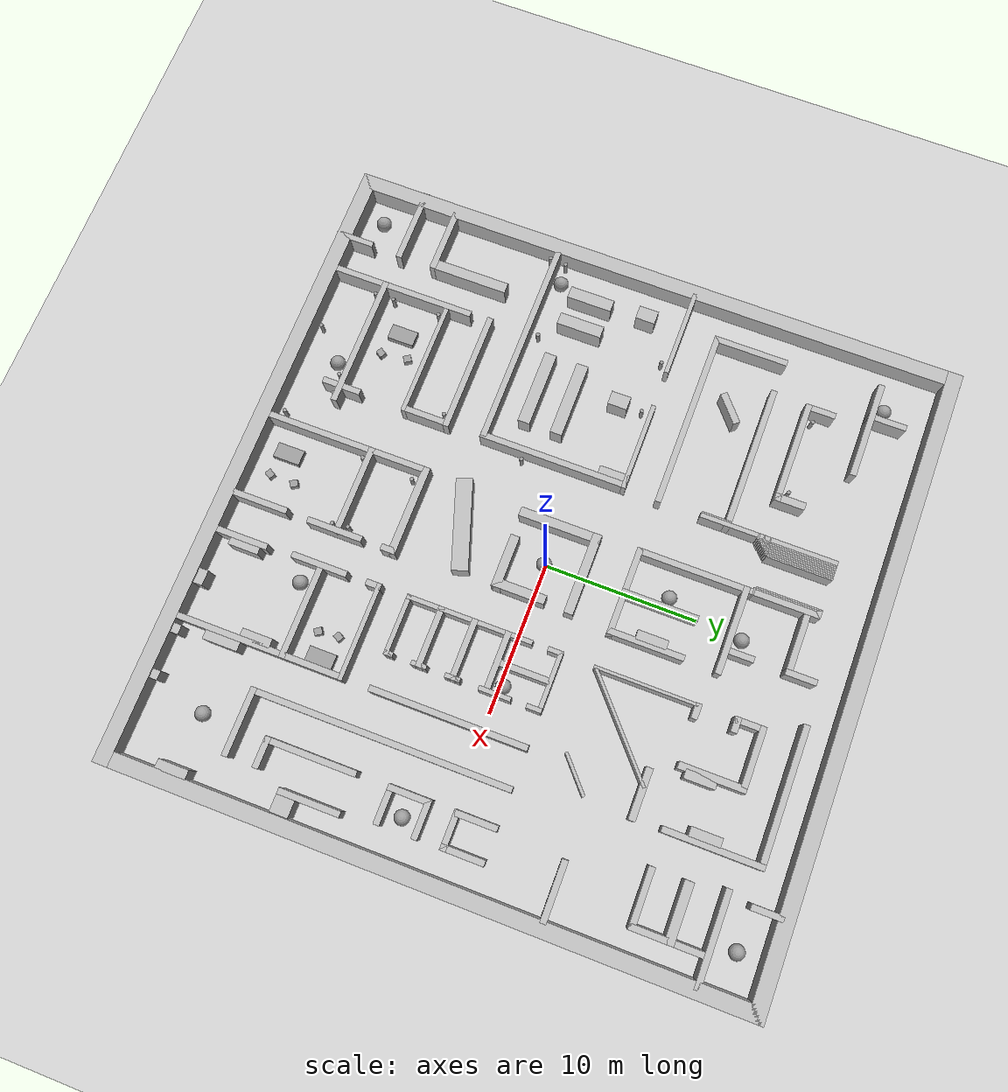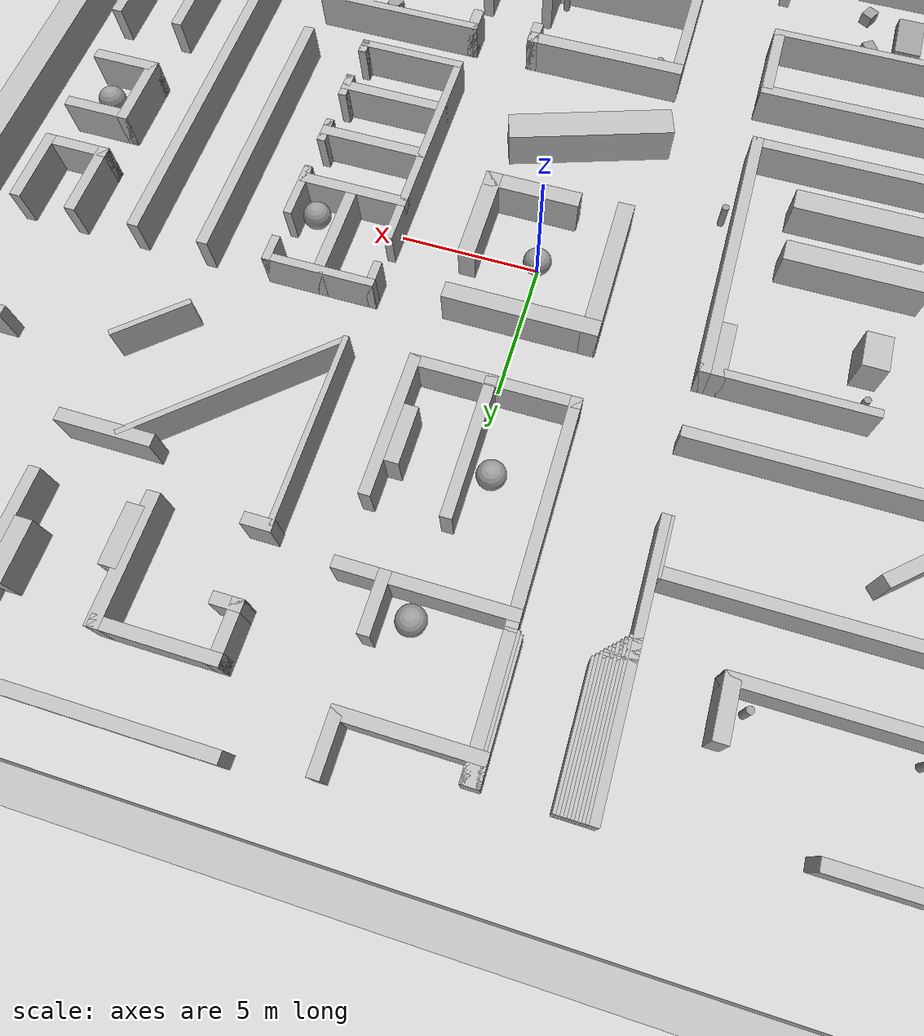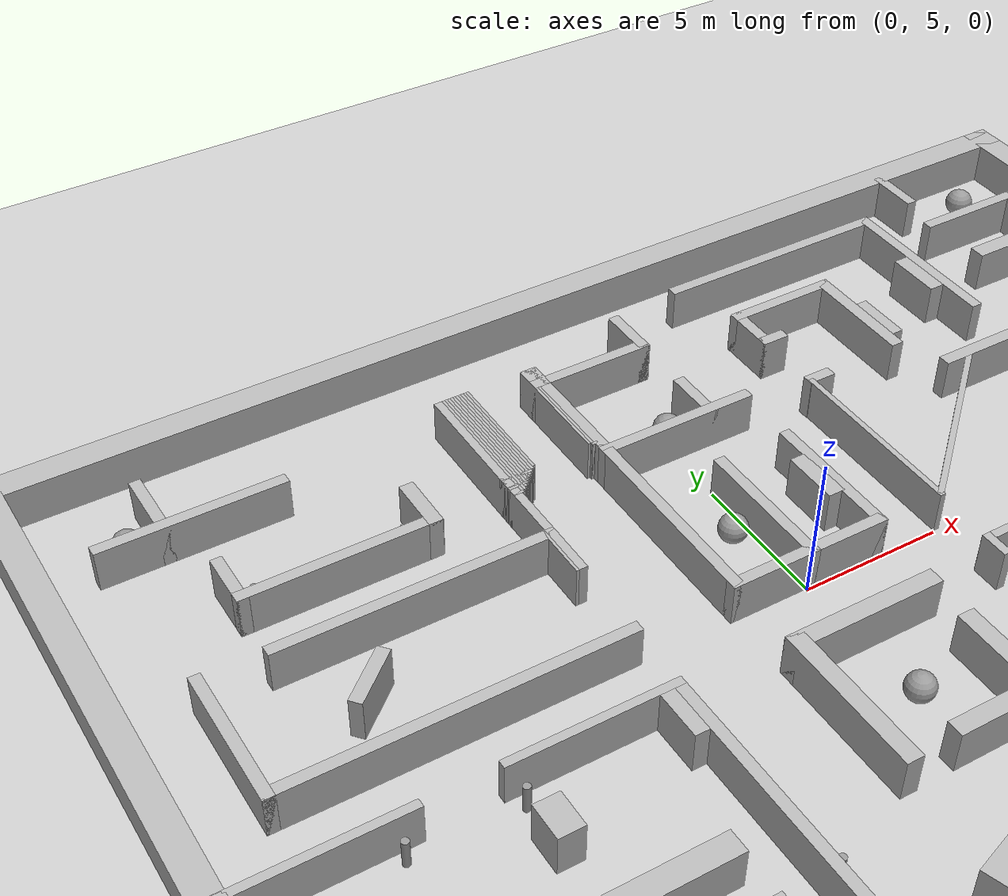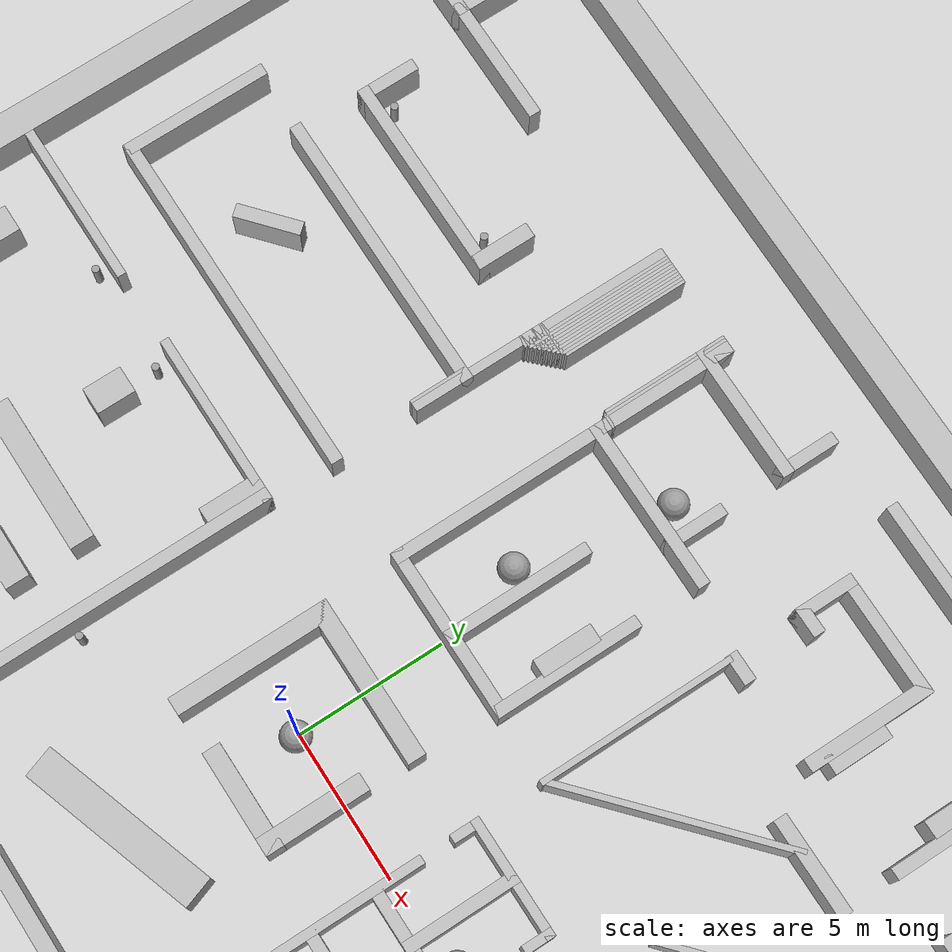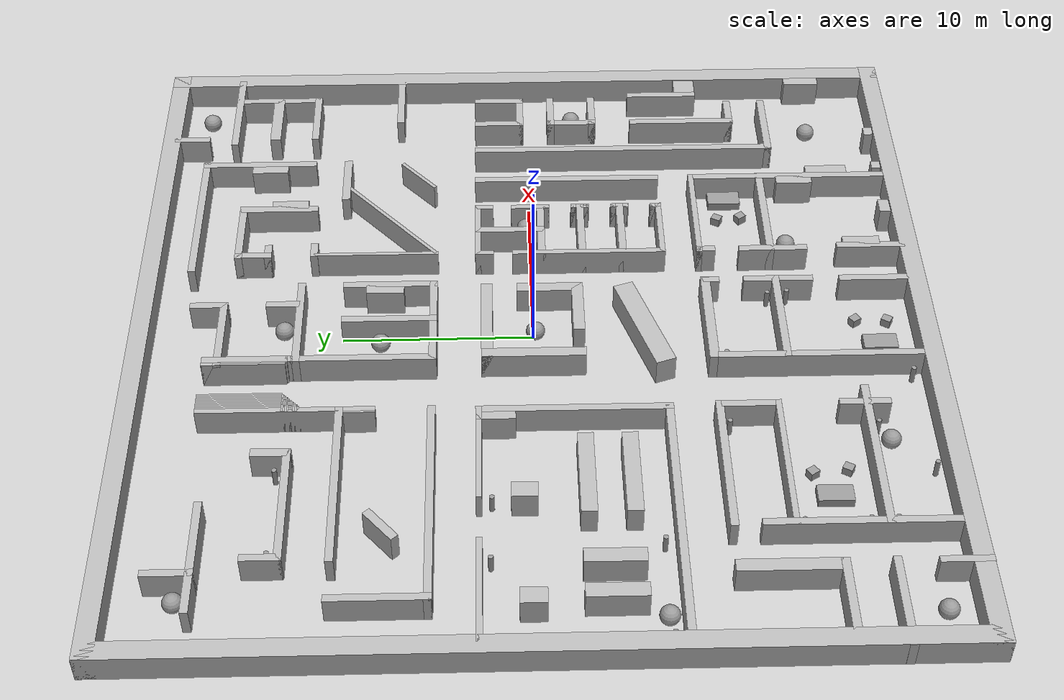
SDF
<sdf version="1.7">
 <world name="test_world">
  <light name="sun" type="directional">
   <pose>0 0 10 0 -0 0</pose>
   <diffuse>0.8 0.8 0.8 1</diffuse>
   <specular>0.2 0.2 0.2 1</specular>
   <attenuation>
    <range>1000</range>
    <constant>0.9</constant>
    <linear>0.01</linear>
    <quadratic>0.001</quadratic>
   </attenuation>
   <direction>-0.5 0.1 -0.9</direction>
   <spot><inner_angle>0</inner_angle><outer_angle>0</outer_angle><falloff>0</falloff></spot>
  </light>
  <model name="ground_plane">
   <static>1</static>
   <link name="link">
    <collision name="collision">
     <geometry><plane><normal>0 0 1</normal><size>100 100</size></plane></geometry>
    </collision>
    <visual name="visual">
     <geometry><plane><normal>0 0 1</normal><size>100 100</size></plane></geometry>
     <material>
      <script>
       <uri>file://media/materials/scripts/gazebo.material</uri>
       <name>__default__</name>
       <n>Gazebo/Grey</n>
      </script>
     </material>
    </visual>
   </link>
  </model>
  <gravity>0 0 -9.8</gravity>
  <physics type="ode">
   <max_step_size>0.001</max_step_size>
   <real_time_factor>1</real_time_factor>
   <real_time_update_rate>1000</real_time_update_rate>
  </physics>
  <scene><ambient>0.4 0.4 0.4 1</ambient><background>0.7 0.7 0.7 1</background><shadows>1</shadows></scene>
  <model name="outer_top">
   <static>1</static>
   <pose>0 20.5 0.75 0 -0 0</pose>
   <link name="link">
    <collision name="collision"><geometry><box><size>42 1 1.5</size></box></geometry></collision>
    <visual name="visual">
     <geometry><box><size>42 1 1.5</size></box></geometry>
     <material>
      <script>
       <uri>file://media/materials/scripts/gazebo.material</uri>
       <name>__default__</name>
       <n>Gazebo/Grey</n>
      </script>
     </material>
    </visual>
   </link>
  </model>
  <model name="outer_bottom">
   <static>1</static>
   <pose>0 -20.5 0.75 0 -0 0</pose>
   <link name="link">
    <collision name="collision"><geometry><box><size>42 1 1.5</size></box></geometry></collision>
    <visual name="visual">
     <geometry><box><size>42 1 1.5</size></box></geometry>
     <material>
      <script>
       <uri>file://media/materials/scripts/gazebo.material</uri>
       <name>__default__</name>
       <n>Gazebo/Grey</n>
      </script>
     </material>
    </visual>
   </link>
  </model>
  <model name="outer_left">
   <static>1</static>
   <pose>-20.5 0 0.75 0 -0 0</pose>
   <link name="link">
    <collision name="collision"><geometry><box><size>1 42 1.5</size></box></geometry></collision>
    <visual name="visual">
     <geometry><box><size>1 42 1.5</size></box></geometry>
     <material>
      <script>
       <uri>file://media/materials/scripts/gazebo.material</uri>
       <name>__default__</name>
       <n>Gazebo/Grey</n>
      </script>
     </material>
    </visual>
   </link>
  </model>
  <model name="outer_right">
   <static>1</static>
   <pose>20.5 0 0.75 0 -0 0</pose>
   <link name="link">
    <collision name="collision"><geometry><box><size>1 42 1.5</size></box></geometry></collision>
    <visual name="visual">
     <geometry><box><size>1 42 1.5</size></box></geometry>
     <material>
      <script>
       <uri>file://media/materials/scripts/gazebo.material</uri>
       <name>__default__</name>
       <n>Gazebo/Grey</n>
      </script>
     </material>
    </visual>
   </link>
  </model>
  <model name="hw_0">
   <static>1</static>
   <pose>-15.3 16.25 0.75 0 -0 0</pose>
   <link name="link">
    <collision name="collision"><geometry><box><size>6.5 0.4 1.5</size></box></geometry></collision>
    <visual name="visual">
     <geometry><box><size>6.5 0.4 1.5</size></box></geometry>
     <material>
      <script>
       <uri>file://media/materials/scripts/gazebo.material</uri>
       <name>__default__</name>
       <n>Gazebo/Grey</n>
      </script>
     </material>
    </visual>
   </link>
  </model>
  <model name="hw_1">
   <static>1</static>
   <pose>-12.05 5.25 0.75 0 -0 0</pose>
   <link name="link">
    <collision name="collision"><geometry><box><size>12 0.4 1.5</size></box></geometry></collision>
    <visual name="visual">
     <geometry><box><size>12 0.4 1.5</size></box></geometry>
     <material>
      <script>
       <uri>file://media/materials/scripts/gazebo.material</uri>
       <name>__default__</name>
       <n>Gazebo/Grey</n>
      </script>
     </material>
    </visual>
   </link>
  </model>
  <model name="hw_2">
   <static>1</static>
   <pose>-10.9 9.85 0.75 0 -0 0</pose>
   <link name="link">
    <collision name="collision"><geometry><box><size>9.7 0.4 1.5</size></box></geometry></collision>
    <visual name="visual">
     <geometry><box><size>9.7 0.4 1.5</size></box></geometry>
     <material>
      <script>
       <uri>file://media/materials/scripts/gazebo.material</uri>
       <name>__default__</name>
       <n>Gazebo/Grey</n>
      </script>
     </material>
    </visual>
   </link>
  </model>
  <model name="hw_3">
   <static>1</static>
   <pose>-12.2 12.25 0.75 0 -0 0</pose>
   <link name="link">
    <collision name="collision"><geometry><box><size>6.9 0.4 1.5</size></box></geometry></collision>
    <visual name="visual">
     <geometry><box><size>6.9 0.4 1.5</size></box></geometry>
     <material>
      <script>
       <uri>file://media/materials/scripts/gazebo.material</uri>
       <name>__default__</name>
       <n>Gazebo/Grey</n>
      </script>
     </material>
    </visual>
   </link>
  </model>
  <model name="hw_4">
   <static>1</static>
   <pose>-13.6 7.55 0.75 0 -0 0.712137</pose>
   <link name="link">
    <collision name="collision"><geometry><box><size>2.16529 0.451675 1.5</size></box></geometry></collision>
    <visual name="visual">
     <geometry><box><size>2.16529 0.451675 1.5</size></box></geometry>
     <material>
      <script>
       <uri>file://media/materials/scripts/gazebo.material</uri>
       <name>__default__</name>
       <n>Gazebo/Grey</n>
      </script>
     </material>
    </visual>
   </link>
  </model>
  <model name="hw_5">
   <static>1</static>
   <pose>-10.05 -9.15 0.75 0 -0 0</pose>
   <link name="link">
    <collision name="collision"><geometry><box><size>8 0.4 1.5</size></box></geometry></collision>
    <visual name="visual">
     <geometry><box><size>8 0.4 1.5</size></box></geometry>
     <material>
      <script>
       <uri>file://media/materials/scripts/gazebo.material</uri>
       <name>__default__</name>
       <n>Gazebo/Grey</n>
      </script>
     </material>
    </visual>
   </link>
  </model>
  <model name="hw_6">
   <static>1</static>
   <pose>-10.05 -12.1 0.75 0 -0 0</pose>
   <link name="link">
    <collision name="collision"><geometry><box><size>8 0.3 1.5</size></box></geometry></collision>
    <visual name="visual">
     <geometry><box><size>8 0.3 1.5</size></box></geometry>
     <material>
      <script>
       <uri>file://media/materials/scripts/gazebo.material</uri>
       <name>__default__</name>
       <n>Gazebo/Grey</n>
      </script>
     </material>
    </visual>
   </link>
  </model>
  <model name="hw_7">
   <static>1</static>
   <pose>-9.6 -16.55 0.75 0 -0 0</pose>
   <link name="link">
    <collision name="collision"><geometry><box><size>8.9 0.4 1.5</size></box></geometry></collision>
    <visual name="visual">
     <geometry><box><size>8.9 0.4 1.5</size></box></geometry>
     <material>
      <script>
       <uri>file://media/materials/scripts/gazebo.material</uri>
       <name>__default__</name>
       <n>Gazebo/Grey</n>
      </script>
     </material>
    </visual>
   </link>
  </model>
  <model name="hw_8">
   <static>1</static>
   <pose>-10.55 -2.35 0.75 0 -0 0</pose>
   <link name="link">
    <collision name="collision"><geometry><box><size>5 0.8 1.5</size></box></geometry></collision>
    <visual name="visual">
     <geometry><box><size>5 0.8 1.5</size></box></geometry>
     <material>
      <script>
       <uri>file://media/materials/scripts/gazebo.material</uri>
       <name>__default__</name>
       <n>Gazebo/Grey</n>
      </script>
     </material>
    </visual>
   </link>
  </model>
  <model name="hw_9">
   <static>1</static>
   <pose>-10.55 -4.55 0.75 0 -0 0</pose>
   <link name="link">
    <collision name="collision"><geometry><box><size>5 0.8 1.5</size></box></geometry></collision>
    <visual name="visual">
     <geometry><box><size>5 0.8 1.5</size></box></geometry>
     <material>
      <script>
       <uri>file://media/materials/scripts/gazebo.material</uri>
       <name>__default__</name>
       <n>Gazebo/Grey</n>
      </script>
     </material>
    </visual>
   </link>
  </model>
  <model name="hw_10">
   <static>1</static>
   <pose>-9.1 2.9 0.75 0 -0 0</pose>
   <link name="link">
    <collision name="collision"><geometry><box><size>5.9 0.3 1.5</size></box></geometry></collision>
    <visual name="visual">
     <geometry><box><size>5.9 0.3 1.5</size></box></geometry>
     <material>
      <script>
       <uri>file://media/materials/scripts/gazebo.material</uri>
       <name>__default__</name>
       <n>Gazebo/Grey</n>
      </script>
     </material>
    </visual>
   </link>
  </model>
  <model name="hw_12">
   <static>1</static>
   <pose>-6.15 11.9 0.75 0 -0 0</pose>
   <link name="link">
    <collision name="collision"><geometry><box><size>0.4 0.1 1.5</size></box></geometry></collision>
    <visual name="visual">
     <geometry><box><size>0.4 0.1 1.5</size></box></geometry>
     <material>
      <script>
       <uri>file://media/materials/scripts/gazebo.material</uri>
       <name>__default__</name>
       <n>Gazebo/Grey</n>
      </script>
     </material>
    </visual>
   </link>
  </model>
  <model name="hw_13">
   <static>1</static>
   <pose>-6.1 12 0.75 0 -0 0</pose>
   <link name="link">
    <collision name="collision"><geometry><box><size>0.5 0.1 1.5</size></box></geometry></collision>
    <visual name="visual">
     <geometry><box><size>0.5 0.1 1.5</size></box></geometry>
     <material>
      <script>
       <uri>file://media/materials/scripts/gazebo.material</uri>
       <name>__default__</name>
       <n>Gazebo/Grey</n>
      </script>
     </material>
    </visual>
   </link>
  </model>
  <model name="hw_14">
   <static>1</static>
   <pose>-6.05 12.1 0.75 0 -0 0</pose>
   <link name="link">
    <collision name="collision"><geometry><box><size>0.6 0.1 1.5</size></box></geometry></collision>
    <visual name="visual">
     <geometry><box><size>0.6 0.1 1.5</size></box></geometry>
     <material>
      <script>
       <uri>file://media/materials/scripts/gazebo.material</uri>
       <name>__default__</name>
       <n>Gazebo/Grey</n>
      </script>
     </material>
    </visual>
   </link>
  </model>
  <model name="hw_15">
   <static>1</static>
   <pose>-6 12.2 0.75 0 -0 0</pose>
   <link name="link">
    <collision name="collision"><geometry><box><size>0.7 0.1 1.5</size></box></geometry></collision>
    <visual name="visual">
     <geometry><box><size>0.7 0.1 1.5</size></box></geometry>
     <material>
      <script>
       <uri>file://media/materials/scripts/gazebo.material</uri>
       <name>__default__</name>
       <n>Gazebo/Grey</n>
      </script>
     </material>
    </visual>
   </link>
  </model>
  <model name="hw_16">
   <static>1</static>
   <pose>-5.95 12.3 0.75 0 -0 0</pose>
   <link name="link">
    <collision name="collision"><geometry><box><size>0.8 0.1 1.5</size></box></geometry></collision>
    <visual name="visual">
     <geometry><box><size>0.8 0.1 1.5</size></box></geometry>
     <material>
      <script>
       <uri>file://media/materials/scripts/gazebo.material</uri>
       <name>__default__</name>
       <n>Gazebo/Grey</n>
      </script>
     </material>
    </visual>
   </link>
  </model>
  <model name="hw_17">
   <static>1</static>
   <pose>-5.9 12.4 0.75 0 -0 0</pose>
   <link name="link">
    <collision name="collision"><geometry><box><size>0.9 0.1 1.5</size></box></geometry></collision>
    <visual name="visual">
     <geometry><box><size>0.9 0.1 1.5</size></box></geometry>
     <material>
      <script>
       <uri>file://media/materials/scripts/gazebo.material</uri>
       <name>__default__</name>
       <n>Gazebo/Grey</n>
      </script>
     </material>
    </visual>
   </link>
  </model>
  <model name="hw_18">
   <static>1</static>
   <pose>-5.85 12.5 0.75 0 -0 0</pose>
   <link name="link">
    <collision name="collision"><geometry><box><size>1 0.1 1.5</size></box></geometry></collision>
    <visual name="visual">
     <geometry><box><size>1 0.1 1.5</size></box></geometry>
     <material>
      <script>
       <uri>file://media/materials/scripts/gazebo.material</uri>
       <name>__default__</name>
       <n>Gazebo/Grey</n>
      </script>
     </material>
    </visual>
   </link>
  </model>
  <model name="hw_19">
   <static>1</static>
   <pose>-5.8 12.6 0.75 0 -0 0</pose>
   <link name="link">
    <collision name="collision"><geometry><box><size>1.1 0.1 1.5</size></box></geometry></collision>
    <visual name="visual">
     <geometry><box><size>1.1 0.1 1.5</size></box></geometry>
     <material>
      <script>
       <uri>file://media/materials/scripts/gazebo.material</uri>
       <name>__default__</name>
       <n>Gazebo/Grey</n>
      </script>
     </material>
    </visual>
   </link>
  </model>
  <model name="hw_20">
   <static>1</static>
   <pose>-5.75 12.7 0.75 0 -0 0</pose>
   <link name="link">
    <collision name="collision"><geometry><box><size>1.2 0.1 1.5</size></box></geometry></collision>
    <visual name="visual">
     <geometry><box><size>1.2 0.1 1.5</size></box></geometry>
     <material>
      <script>
       <uri>file://media/materials/scripts/gazebo.material</uri>
       <name>__default__</name>
       <n>Gazebo/Grey</n>
      </script>
     </material>
    </visual>
   </link>
  </model>
  <model name="hw_21">
   <static>1</static>
   <pose>-2.75 16.75 0.75 0 -0 0</pose>
   <link name="link">
    <collision name="collision"><geometry><box><size>0.6 0.6 1.5</size></box></geometry></collision>
    <visual name="visual">
     <geometry><box><size>0.6 0.6 1.5</size></box></geometry>
     <material>
      <script>
       <uri>file://media/materials/scripts/gazebo.material</uri>
       <name>__default__</name>
       <n>Gazebo/Grey</n>
      </script>
     </material>
    </visual>
   </link>
  </model>
  <model name="hw_22">
   <static>1</static>
   <pose>-0.75 16.25 0.75 0 -0 0</pose>
   <link name="link">
    <collision name="collision"><geometry><box><size>4.6 0.4 1.5</size></box></geometry></collision>
    <visual name="visual">
     <geometry><box><size>4.6 0.4 1.5</size></box></geometry>
     <material>
      <script>
       <uri>file://media/materials/scripts/gazebo.material</uri>
       <name>__default__</name>
       <n>Gazebo/Grey</n>
      </script>
     </material>
    </visual>
   </link>
  </model>
  <model name="hw_23">
   <static>1</static>
   <pose>-0.380805 -5.75282 0.75 0 -0 0.325273</pose>
   <link name="link">
    <collision name="collision"><geometry><box><size>6 1.07714 1.5</size></box></geometry></collision>
    <visual name="visual">
     <geometry><box><size>6 1.07714 1.5</size></box></geometry>
     <material>
      <script>
       <uri>file://media/materials/scripts/gazebo.material</uri>
       <name>__default__</name>
       <n>Gazebo/Grey</n>
      </script>
     </material>
    </visual>
   </link>
  </model>
  <model name="hw_24">
   <static>1</static>
   <pose>-0.05 -9.2 0.75 0 -0 0</pose>
   <link name="link">
    <collision name="collision"><geometry><box><size>6 0.5 1.5</size></box></geometry></collision>
    <visual name="visual">
     <geometry><box><size>6 0.5 1.5</size></box></geometry>
     <material>
      <script>
       <uri>file://media/materials/scripts/gazebo.material</uri>
       <name>__default__</name>
       <n>Gazebo/Grey</n>
      </script>
     </material>
    </visual>
   </link>
  </model>
  <model name="hw_25">
   <static>1</static>
   <pose>-0.05 -12.95 0.75 0 -0 0</pose>
   <link name="link">
    <collision name="collision"><geometry><box><size>6 0.4 1.5</size></box></geometry></collision>
    <visual name="visual">
     <geometry><box><size>6 0.4 1.5</size></box></geometry>
     <material>
      <script>
       <uri>file://media/materials/scripts/gazebo.material</uri>
       <name>__default__</name>
       <n>Gazebo/Grey</n>
      </script>
     </material>
    </visual>
   </link>
  </model>
  <model name="hw_26">
   <static>1</static>
   <pose>-2.7 12.7 0.75 0 -0 0</pose>
   <link name="link">
    <collision name="collision"><geometry><box><size>0.5 0.1 1.5</size></box></geometry></collision>
    <visual name="visual">
     <geometry><box><size>0.5 0.1 1.5</size></box></geometry>
     <material>
      <script>
       <uri>file://media/materials/scripts/gazebo.material</uri>
       <name>__default__</name>
       <n>Gazebo/Grey</n>
      </script>
     </material>
    </visual>
   </link>
  </model>
  <model name="hw_27">
   <static>1</static>
   <pose>-2.65 12.55 0.75 0 -0 0</pose>
   <link name="link">
    <collision name="collision"><geometry><box><size>0.4 0.2 1.5</size></box></geometry></collision>
    <visual name="visual">
     <geometry><box><size>0.4 0.2 1.5</size></box></geometry>
     <material>
      <script>
       <uri>file://media/materials/scripts/gazebo.material</uri>
       <name>__default__</name>
       <n>Gazebo/Grey</n>
      </script>
     </material>
    </visual>
   </link>
  </model>
  <model name="hw_28">
   <static>1</static>
   <pose>0.05 12.25 0.75 0 -0 0</pose>
   <link name="link">
    <collision name="collision"><geometry><box><size>5.8 0.4 1.5</size></box></geometry></collision>
    <visual name="visual">
     <geometry><box><size>5.8 0.4 1.5</size></box></geometry>
     <material>
      <script>
       <uri>file://media/materials/scripts/gazebo.material</uri>
       <name>__default__</name>
       <n>Gazebo/Grey</n>
      </script>
     </material>
    </visual>
   </link>
  </model>
  <model name="hw_29">
   <static>1</static>
   <pose>0.05 5.25 0.75 0 -0 0</pose>
   <link name="link">
    <collision name="collision"><geometry><box><size>5.8 0.4 1.5</size></box></geometry></collision>
    <visual name="visual">
     <geometry><box><size>5.8 0.4 1.5</size></box></geometry>
     <material>
      <script>
       <uri>file://media/materials/scripts/gazebo.material</uri>
       <name>__default__</name>
       <n>Gazebo/Grey</n>
      </script>
     </material>
    </visual>
   </link>
  </model>
  <model name="hw_30">
   <static>1</static>
   <pose>-0.05 2.45 0.75 0 -0 0</pose>
   <link name="link">
    <collision name="collision"><geometry><box><size>5.4 0.6 1.5</size></box></geometry></collision>
    <visual name="visual">
     <geometry><box><size>5.4 0.6 1.5</size></box></geometry>
     <material>
      <script>
       <uri>file://media/materials/scripts/gazebo.material</uri>
       <name>__default__</name>
       <n>Gazebo/Grey</n>
      </script>
     </material>
    </visual>
   </link>
  </model>
  <model name="hw_31">
   <static>1</static>
   <pose>0.9 -2.35 0.75 0 -0 0</pose>
   <link name="link">
    <collision name="collision"><geometry><box><size>3.5 0.6 1.5</size></box></geometry></collision>
    <visual name="visual">
     <geometry><box><size>3.5 0.6 1.5</size></box></geometry>
     <material>
      <script>
       <uri>file://media/materials/scripts/gazebo.material</uri>
       <name>__default__</name>
       <n>Gazebo/Grey</n>
      </script>
     </material>
    </visual>
   </link>
  </model>
  <model name="hw_32">
   <static>1</static>
   <pose>8.45 18.25 0.75 0 -0 0</pose>
   <link name="link">
    <collision name="collision"><geometry><box><size>9 0.4 1.5</size></box></geometry></collision>
    <visual name="visual">
     <geometry><box><size>9 0.4 1.5</size></box></geometry>
     <material>
      <script>
       <uri>file://media/materials/scripts/gazebo.material</uri>
       <name>__default__</name>
       <n>Gazebo/Grey</n>
      </script>
     </material>
    </visual>
   </link>
  </model>
  <model name="hw_46">
   <static>1</static>
   <pose>5.45 14.25 0.75 0 -0 0</pose>
   <link name="link">
    <collision name="collision"><geometry><box><size>1 0.4 1.5</size></box></geometry></collision>
    <visual name="visual">
     <geometry><box><size>1 0.4 1.5</size></box></geometry>
     <material>
      <script>
       <uri>file://media/materials/scripts/gazebo.material</uri>
       <name>__default__</name>
       <n>Gazebo/Grey</n>
      </script>
     </material>
    </visual>
   </link>
  </model>
  <model name="hw_47">
   <static>1</static>
   <pose>6.95 2.9 0.75 0 -0 0</pose>
   <link name="link">
    <collision name="collision"><geometry><box><size>4 0.3 1.5</size></box></geometry></collision>
    <visual name="visual">
     <geometry><box><size>4 0.3 1.5</size></box></geometry>
     <material>
      <script>
       <uri>file://media/materials/scripts/gazebo.material</uri>
       <name>__default__</name>
       <n>Gazebo/Grey</n>
      </script>
     </material>
    </visual>
   </link>
  </model>
  <model name="hw_48">
   <static>1</static>
   <pose>6.95 -0.55 0.75 0 -0 0</pose>
   <link name="link">
    <collision name="collision"><geometry><box><size>4 0.4 1.5</size></box></geometry></collision>
    <visual name="visual">
     <geometry><box><size>4 0.4 1.5</size></box></geometry>
     <material>
      <script>
       <uri>file://media/materials/scripts/gazebo.material</uri>
       <name>__default__</name>
       <n>Gazebo/Grey</n>
      </script>
     </material>
    </visual>
   </link>
  </model>
  <model name="hw_49">
   <static>1</static>
   <pose>6.95 -2.75 0.75 0 -0 0</pose>
   <link name="link">
    <collision name="collision"><geometry><box><size>4 0.4 1.5</size></box></geometry></collision>
    <visual name="visual">
     <geometry><box><size>4 0.4 1.5</size></box></geometry>
     <material>
      <script>
       <uri>file://media/materials/scripts/gazebo.material</uri>
       <name>__default__</name>
       <n>Gazebo/Grey</n>
      </script>
     </material>
    </visual>
   </link>
  </model>
  <model name="hw_50">
   <static>1</static>
   <pose>6.95 -4.95 0.75 0 -0 0</pose>
   <link name="link">
    <collision name="collision"><geometry><box><size>4 0.4 1.5</size></box></geometry></collision>
    <visual name="visual">
     <geometry><box><size>4 0.4 1.5</size></box></geometry>
     <material>
      <script>
       <uri>file://media/materials/scripts/gazebo.material</uri>
       <name>__default__</name>
       <n>Gazebo/Grey</n>
      </script>
     </material>
    </visual>
   </link>
  </model>
  <model name="hw_51">
   <static>1</static>
   <pose>6.95 -7.1 0.75 0 -0 0</pose>
   <link name="link">
    <collision name="collision"><geometry><box><size>4 0.3 1.5</size></box></geometry></collision>
    <visual name="visual">
     <geometry><box><size>4 0.3 1.5</size></box></geometry>
     <material>
      <script>
       <uri>file://media/materials/scripts/gazebo.material</uri>
       <name>__default__</name>
       <n>Gazebo/Grey</n>
      </script>
     </material>
    </visual>
   </link>
  </model>
  <model name="hw_52">
   <static>1</static>
   <pose>7 15.85 0.75 0 -0 0</pose>
   <link name="link">
    <collision name="collision"><geometry><box><size>4.1 0.4 1.5</size></box></geometry></collision>
    <visual name="visual">
     <geometry><box><size>4.1 0.4 1.5</size></box></geometry>
     <material>
      <script>
       <uri>file://media/materials/scripts/gazebo.material</uri>
       <name>__default__</name>
       <n>Gazebo/Grey</n>
      </script>
     </material>
    </visual>
   </link>
  </model>
  <model name="hw_53">
   <static>1</static>
   <pose>8.15 -9.1 0.75 0 -0 0</pose>
   <link name="link">
    <collision name="collision"><geometry><box><size>6.4 0.3 1.5</size></box></geometry></collision>
    <visual name="visual">
     <geometry><box><size>6.4 0.3 1.5</size></box></geometry>
     <material>
      <script>
       <uri>file://media/materials/scripts/gazebo.material</uri>
       <name>__default__</name>
       <n>Gazebo/Grey</n>
      </script>
     </material>
    </visual>
   </link>
  </model>
  <model name="hw_54">
   <static>1</static>
   <pose>8.15 -12.95 0.75 0 -0 0</pose>
   <link name="link">
    <collision name="collision"><geometry><box><size>6.4 0.4 1.5</size></box></geometry></collision>
    <visual name="visual">
     <geometry><box><size>6.4 0.4 1.5</size></box></geometry>
     <material>
      <script>
       <uri>file://media/materials/scripts/gazebo.material</uri>
       <name>__default__</name>
       <n>Gazebo/Grey</n>
      </script>
     </material>
    </visual>
   </link>
  </model>
  <model name="hw_94">
   <static>1</static>
   <pose>8.45 -19.65 0.75 0 -0 0</pose>
   <link name="link">
    <collision name="collision"><geometry><box><size>1 0.6 1.5</size></box></geometry></collision>
    <visual name="visual">
     <geometry><box><size>1 0.6 1.5</size></box></geometry>
     <material>
      <script>
       <uri>file://media/materials/scripts/gazebo.material</uri>
       <name>__default__</name>
       <n>Gazebo/Grey</n>
      </script>
     </material>
    </visual>
   </link>
  </model>
  <model name="hw_104">
   <static>1</static>
   <pose>8.8 -0.9 0.75 0 -0 0</pose>
   <link name="link">
    <collision name="collision"><geometry><box><size>0.3 0.3 1.5</size></box></geometry></collision>
    <visual name="visual">
     <geometry><box><size>0.3 0.3 1.5</size></box></geometry>
     <material>
      <script>
       <uri>file://media/materials/scripts/gazebo.material</uri>
       <name>__default__</name>
       <n>Gazebo/Grey</n>
      </script>
     </material>
    </visual>
   </link>
  </model>
  <model name="hw_105">
   <static>1</static>
   <pose>8.8 -2.4 0.75 0 -0 0</pose>
   <link name="link">
    <collision name="collision"><geometry><box><size>0.3 0.3 1.5</size></box></geometry></collision>
    <visual name="visual">
     <geometry><box><size>0.3 0.3 1.5</size></box></geometry>
     <material>
      <script>
       <uri>file://media/materials/scripts/gazebo.material</uri>
       <name>__default__</name>
       <n>Gazebo/Grey</n>
      </script>
     </material>
    </visual>
   </link>
  </model>
  <model name="hw_106">
   <static>1</static>
   <pose>8.8 -3.1 0.75 0 -0 0</pose>
   <link name="link">
    <collision name="collision"><geometry><box><size>0.3 0.3 1.5</size></box></geometry></collision>
    <visual name="visual">
     <geometry><box><size>0.3 0.3 1.5</size></box></geometry>
     <material>
      <script>
       <uri>file://media/materials/scripts/gazebo.material</uri>
       <name>__default__</name>
       <n>Gazebo/Grey</n>
      </script>
     </material>
    </visual>
   </link>
  </model>
  <model name="hw_107">
   <static>1</static>
   <pose>8.8 -4.6 0.75 0 -0 0</pose>
   <link name="link">
    <collision name="collision"><geometry><box><size>0.3 0.3 1.5</size></box></geometry></collision>
    <visual name="visual">
     <geometry><box><size>0.3 0.3 1.5</size></box></geometry>
     <material>
      <script>
       <uri>file://media/materials/scripts/gazebo.material</uri>
       <name>__default__</name>
       <n>Gazebo/Grey</n>
      </script>
     </material>
    </visual>
   </link>
  </model>
  <model name="hw_108">
   <static>1</static>
   <pose>8.8 -5.3 0.75 0 -0 0</pose>
   <link name="link">
    <collision name="collision"><geometry><box><size>0.3 0.3 1.5</size></box></geometry></collision>
    <visual name="visual">
     <geometry><box><size>0.3 0.3 1.5</size></box></geometry>
     <material>
      <script>
       <uri>file://media/materials/scripts/gazebo.material</uri>
       <name>__default__</name>
       <n>Gazebo/Grey</n>
      </script>
     </material>
    </visual>
   </link>
  </model>
  <model name="hw_109">
   <static>1</static>
   <pose>8.8 -6.8 0.75 0 -0 0</pose>
   <link name="link">
    <collision name="collision"><geometry><box><size>0.3 0.3 1.5</size></box></geometry></collision>
    <visual name="visual">
     <geometry><box><size>0.3 0.3 1.5</size></box></geometry>
     <material>
      <script>
       <uri>file://media/materials/scripts/gazebo.material</uri>
       <name>__default__</name>
       <n>Gazebo/Grey</n>
      </script>
     </material>
    </visual>
   </link>
  </model>
  <model name="hw_121">
   <static>1</static>
   <pose>11.3 10.2356 0.75 0 -0 0</pose>
   <link name="link">
    <collision name="collision"><geometry><box><size>3.3 0.447718 1.5</size></box></geometry></collision>
    <visual name="visual">
     <geometry><box><size>3.3 0.447718 1.5</size></box></geometry>
     <material>
      <script>
       <uri>file://media/materials/scripts/gazebo.material</uri>
       <name>__default__</name>
       <n>Gazebo/Grey</n>
      </script>
     </material>
    </visual>
   </link>
  </model>
  <model name="hw_122">
   <static>1</static>
   <pose>11.95 -19.7 0.75 0 -0 0</pose>
   <link name="link">
    <collision name="collision"><geometry><box><size>0.6 0.5 1.5</size></box></geometry></collision>
    <visual name="visual">
     <geometry><box><size>0.6 0.5 1.5</size></box></geometry>
     <material>
      <script>
       <uri>file://media/materials/scripts/gazebo.material</uri>
       <name>__default__</name>
       <n>Gazebo/Grey</n>
      </script>
     </material>
    </visual>
   </link>
  </model>
  <model name="hw_123">
   <static>1</static>
   <pose>15.75 -13.75 0.75 0 -0 0</pose>
   <link name="link">
    <collision name="collision"><geometry><box><size>4.4 0.4 1.5</size></box></geometry></collision>
    <visual name="visual">
     <geometry><box><size>4.4 0.4 1.5</size></box></geometry>
     <material>
      <script>
       <uri>file://media/materials/scripts/gazebo.material</uri>
       <name>__default__</name>
       <n>Gazebo/Grey</n>
      </script>
     </material>
    </visual>
   </link>
  </model>
  <model name="hw_124">
   <static>1</static>
   <pose>14.95 -19.7 0.75 0 -0 0</pose>
   <link name="link">
    <collision name="collision"><geometry><box><size>0.6 0.5 1.5</size></box></geometry></collision>
    <visual name="visual">
     <geometry><box><size>0.6 0.5 1.5</size></box></geometry>
     <material>
      <script>
       <uri>file://media/materials/scripts/gazebo.material</uri>
       <name>__default__</name>
       <n>Gazebo/Grey</n>
      </script>
     </material>
    </visual>
   </link>
  </model>
  <model name="hw_125">
   <static>1</static>
   <pose>17.5122 16.85 0.75 0 -0 0</pose>
   <link name="link">
    <collision name="collision"><geometry><box><size>5.93657 0.4 1.5</size></box></geometry></collision>
    <visual name="visual">
     <geometry><box><size>5.93657 0.4 1.5</size></box></geometry>
     <material>
      <script>
       <uri>file://media/materials/scripts/gazebo.material</uri>
       <name>__default__</name>
       <n>Gazebo/Grey</n>
      </script>
     </material>
    </visual>
   </link>
  </model>
  <model name="hw_126">
   <static>1</static>
   <pose>16.85 14.55 0.75 0 -0 0</pose>
   <link name="link">
    <collision name="collision"><geometry><box><size>3.8 0.6 1.5</size></box></geometry></collision>
    <visual name="visual">
     <geometry><box><size>3.8 0.6 1.5</size></box></geometry>
     <material>
      <script>
       <uri>file://media/materials/scripts/gazebo.material</uri>
       <name>__default__</name>
       <n>Gazebo/Grey</n>
      </script>
     </material>
    </visual>
   </link>
  </model>
  <model name="hw_127">
   <static>1</static>
   <pose>16.85 12.25 0.75 0 -0 0</pose>
   <link name="link">
    <collision name="collision"><geometry><box><size>3.8 0.4 1.5</size></box></geometry></collision>
    <visual name="visual">
     <geometry><box><size>3.8 0.4 1.5</size></box></geometry>
     <material>
      <script>
       <uri>file://media/materials/scripts/gazebo.material</uri>
       <name>__default__</name>
       <n>Gazebo/Grey</n>
      </script>
     </material>
    </visual>
   </link>
  </model>
  <model name="hw_128">
   <static>1</static>
   <pose>16.95 -11.75 0.75 0 -0 0</pose>
   <link name="link">
    <collision name="collision"><geometry><box><size>2 0.4 1.5</size></box></geometry></collision>
    <visual name="visual">
     <geometry><box><size>2 0.4 1.5</size></box></geometry>
     <material>
      <script>
       <uri>file://media/materials/scripts/gazebo.material</uri>
       <name>__default__</name>
       <n>Gazebo/Grey</n>
      </script>
     </material>
    </visual>
   </link>
  </model>
  <model name="hw_129">
   <static>1</static>
   <pose>17.2 0.45 0.75 0 -0 0</pose>
   <link name="link">
    <collision name="collision"><geometry><box><size>2.5 0.4 1.5</size></box></geometry></collision>
    <visual name="visual">
     <geometry><box><size>2.5 0.4 1.5</size></box></geometry>
     <material>
      <script>
       <uri>file://media/materials/scripts/gazebo.material</uri>
       <name>__default__</name>
       <n>Gazebo/Grey</n>
      </script>
     </material>
    </visual>
   </link>
  </model>
  <model name="hw_130">
   <static>1</static>
   <pose>17.2 -1.35 0.75 0 -0 0</pose>
   <link name="link">
    <collision name="collision"><geometry><box><size>2.5 0.4 1.5</size></box></geometry></collision>
    <visual name="visual">
     <geometry><box><size>2.5 0.4 1.5</size></box></geometry>
     <material>
      <script>
       <uri>file://media/materials/scripts/gazebo.material</uri>
       <name>__default__</name>
       <n>Gazebo/Grey</n>
      </script>
     </material>
    </visual>
   </link>
  </model>
  <model name="hw_131">
   <static>1</static>
   <pose>17.2 -3.75 0.75 0 -0 0</pose>
   <link name="link">
    <collision name="collision"><geometry><box><size>2.5 0.4 1.5</size></box></geometry></collision>
    <visual name="visual">
     <geometry><box><size>2.5 0.4 1.5</size></box></geometry>
     <material>
      <script>
       <uri>file://media/materials/scripts/gazebo.material</uri>
       <name>__default__</name>
       <n>Gazebo/Grey</n>
      </script>
     </material>
    </visual>
   </link>
  </model>
  <model name="vw_132">
   <static>1</static>
   <pose>-16.25 17.3 0.75 0 -0 0</pose>
   <link name="link">
    <collision name="collision"><geometry><box><size>0.4 2.5 1.5</size></box></geometry></collision>
    <visual name="visual">
     <geometry><box><size>0.4 2.5 1.5</size></box></geometry>
     <material>
      <script>
       <uri>file://media/materials/scripts/gazebo.material</uri>
       <name>__default__</name>
       <n>Gazebo/Grey</n>
      </script>
     </material>
    </visual>
   </link>
  </model>
  <model name="vw_133">
   <static>1</static>
   <pose>12.75 15.25 0.75 0 -0 0</pose>
   <link name="link">
    <collision name="collision"><geometry><box><size>0.4 6.4 1.5</size></box></geometry></collision>
    <visual name="visual">
     <geometry><box><size>0.4 6.4 1.5</size></box></geometry>
     <material>
      <script>
       <uri>file://media/materials/scripts/gazebo.material</uri>
       <name>__default__</name>
       <n>Gazebo/Grey</n>
      </script>
     </material>
    </visual>
   </link>
  </model>
  <model name="vw_134">
   <static>1</static>
   <pose>1.35 17.05 0.75 0 -0 0</pose>
   <link name="link">
    <collision name="collision"><geometry><box><size>0.4 2 1.5</size></box></geometry></collision>
    <visual name="visual">
     <geometry><box><size>0.4 2 1.5</size></box></geometry>
     <material>
      <script>
       <uri>file://media/materials/scripts/gazebo.material</uri>
       <name>__default__</name>
       <n>Gazebo/Grey</n>
      </script>
     </material>
    </visual>
   </link>
  </model>
  <model name="vw_135">
   <static>1</static>
   <pose>-5.1 14.9 0.75 0 -0 0</pose>
   <link name="link">
    <collision name="collision"><geometry><box><size>0.1 4.3 1.5</size></box></geometry></collision>
    <visual name="visual">
     <geometry><box><size>0.1 4.3 1.5</size></box></geometry>
     <material>
      <script>
       <uri>file://media/materials/scripts/gazebo.material</uri>
       <name>__default__</name>
       <n>Gazebo/Grey</n>
      </script>
     </material>
    </visual>
   </link>
  </model>
  <model name="vw_136">
   <static>1</static>
   <pose>-3 14.9 0.75 0 -0 0</pose>
   <link name="link">
    <collision name="collision"><geometry><box><size>0.1 4.3 1.5</size></box></geometry></collision>
    <visual name="visual">
     <geometry><box><size>0.1 4.3 1.5</size></box></geometry>
     <material>
      <script>
       <uri>file://media/materials/scripts/gazebo.material</uri>
       <name>__default__</name>
       <n>Gazebo/Grey</n>
      </script>
     </material>
    </visual>
   </link>
  </model>
  <model name="vw_137">
   <static>1</static>
   <pose>-5.2 14.85 0.75 0 -0 0</pose>
   <link name="link">
    <collision name="collision"><geometry><box><size>0.1 4.4 1.5</size></box></geometry></collision>
    <visual name="visual">
     <geometry><box><size>0.1 4.4 1.5</size></box></geometry>
     <material>
      <script>
       <uri>file://media/materials/scripts/gazebo.material</uri>
       <name>__default__</name>
       <n>Gazebo/Grey</n>
      </script>
     </material>
    </visual>
   </link>
  </model>
  <model name="vw_138">
   <static>1</static>
   <pose>-2.9 14.85 0.75 0 -0 0</pose>
   <link name="link">
    <collision name="collision"><geometry><box><size>0.1 4.4 1.5</size></box></geometry></collision>
    <visual name="visual">
     <geometry><box><size>0.1 4.4 1.5</size></box></geometry>
     <material>
      <script>
       <uri>file://media/materials/scripts/gazebo.material</uri>
       <name>__default__</name>
       <n>Gazebo/Grey</n>
      </script>
     </material>
    </visual>
   </link>
  </model>
  <model name="vw_139">
   <static>1</static>
   <pose>-5.3 14.8 0.75 0 -0 0</pose>
   <link name="link">
    <collision name="collision"><geometry><box><size>0.1 4.5 1.5</size></box></geometry></collision>
    <visual name="visual">
     <geometry><box><size>0.1 4.5 1.5</size></box></geometry>
     <material>
      <script>
       <uri>file://media/materials/scripts/gazebo.material</uri>
       <name>__default__</name>
       <n>Gazebo/Grey</n>
      </script>
     </material>
    </visual>
   </link>
  </model>
  <model name="vw_140">
   <static>1</static>
   <pose>-5.4 14.75 0.75 0 -0 0</pose>
   <link name="link">
    <collision name="collision"><geometry><box><size>0.1 4.6 1.5</size></box></geometry></collision>
    <visual name="visual">
     <geometry><box><size>0.1 4.6 1.5</size></box></geometry>
     <material>
      <script>
       <uri>file://media/materials/scripts/gazebo.material</uri>
       <name>__default__</name>
       <n>Gazebo/Grey</n>
      </script>
     </material>
    </visual>
   </link>
  </model>
  <model name="vw_141">
   <static>1</static>
   <pose>-5.5 14.7 0.75 0 -0 0</pose>
   <link name="link">
    <collision name="collision"><geometry><box><size>0.1 4.7 1.5</size></box></geometry></collision>
    <visual name="visual">
     <geometry><box><size>0.1 4.7 1.5</size></box></geometry>
     <material>
      <script>
       <uri>file://media/materials/scripts/gazebo.material</uri>
       <name>__default__</name>
       <n>Gazebo/Grey</n>
      </script>
     </material>
    </visual>
   </link>
  </model>
  <model name="vw_142">
   <static>1</static>
   <pose>-5.6 14.65 0.75 0 -0 0</pose>
   <link name="link">
    <collision name="collision"><geometry><box><size>0.1 4.8 1.5</size></box></geometry></collision>
    <visual name="visual">
     <geometry><box><size>0.1 4.8 1.5</size></box></geometry>
     <material>
      <script>
       <uri>file://media/materials/scripts/gazebo.material</uri>
       <name>__default__</name>
       <n>Gazebo/Grey</n>
      </script>
     </material>
    </visual>
   </link>
  </model>
  <model name="vw_143">
   <static>1</static>
   <pose>-5.7 14.6 0.75 0 -0 0</pose>
   <link name="link">
    <collision name="collision"><geometry><box><size>0.1 4.9 1.5</size></box></geometry></collision>
    <visual name="visual">
     <geometry><box><size>0.1 4.9 1.5</size></box></geometry>
     <material>
      <script>
       <uri>file://media/materials/scripts/gazebo.material</uri>
       <name>__default__</name>
       <n>Gazebo/Grey</n>
      </script>
     </material>
    </visual>
   </link>
  </model>
  <model name="vw_144">
   <static>1</static>
   <pose>-5.8 14.55 0.75 0 -0 0</pose>
   <link name="link">
    <collision name="collision"><geometry><box><size>0.1 5 1.5</size></box></geometry></collision>
    <visual name="visual">
     <geometry><box><size>0.1 5 1.5</size></box></geometry>
     <material>
      <script>
       <uri>file://media/materials/scripts/gazebo.material</uri>
       <name>__default__</name>
       <n>Gazebo/Grey</n>
      </script>
     </material>
    </visual>
   </link>
  </model>
  <model name="vw_145">
   <static>1</static>
   <pose>18.55 14.55 0.75 0 -0 0</pose>
   <link name="link">
    <collision name="collision"><geometry><box><size>0.4 5 1.5</size></box></geometry></collision>
    <visual name="visual">
     <geometry><box><size>0.4 5 1.5</size></box></geometry>
     <material>
      <script>
       <uri>file://media/materials/scripts/gazebo.material</uri>
       <name>__default__</name>
       <n>Gazebo/Grey</n>
      </script>
     </material>
    </visual>
   </link>
  </model>
  <model name="vw_146">
   <static>1</static>
   <pose>-5.9 14.5 0.75 0 -0 0</pose>
   <link name="link">
    <collision name="collision"><geometry><box><size>0.1 5.1 1.5</size></box></geometry></collision>
    <visual name="visual">
     <geometry><box><size>0.1 5.1 1.5</size></box></geometry>
     <material>
      <script>
       <uri>file://media/materials/scripts/gazebo.material</uri>
       <name>__default__</name>
       <n>Gazebo/Grey</n>
      </script>
     </material>
    </visual>
   </link>
  </model>
  <model name="vw_147">
   <static>1</static>
   <pose>-6 14.45 0.75 0 -0 0</pose>
   <link name="link">
    <collision name="collision"><geometry><box><size>0.1 5.2 1.5</size></box></geometry></collision>
    <visual name="visual">
     <geometry><box><size>0.1 5.2 1.5</size></box></geometry>
     <material>
      <script>
       <uri>file://media/materials/scripts/gazebo.material</uri>
       <name>__default__</name>
       <n>Gazebo/Grey</n>
      </script>
     </material>
    </visual>
   </link>
  </model>
  <model name="vw_148">
   <static>1</static>
   <pose>-6.2 12.55 0.75 0 -0 0</pose>
   <link name="link">
    <collision name="collision"><geometry><box><size>0.3 9 1.5</size></box></geometry></collision>
    <visual name="visual">
     <geometry><box><size>0.3 9 1.5</size></box></geometry>
     <material>
      <script>
       <uri>file://media/materials/scripts/gazebo.material</uri>
       <name>__default__</name>
       <n>Gazebo/Grey</n>
      </script>
     </material>
    </visual>
   </link>
  </model>
  <model name="vw_149">
   <static>1</static>
   <pose>-2.65 11.05 0.75 0 -0 0</pose>
   <link name="link">
    <collision name="collision"><geometry><box><size>0.4 12 1.5</size></box></geometry></collision>
    <visual name="visual">
     <geometry><box><size>0.4 12 1.5</size></box></geometry>
     <material>
      <script>
       <uri>file://media/materials/scripts/gazebo.material</uri>
       <name>__default__</name>
       <n>Gazebo/Grey</n>
      </script>
     </material>
    </visual>
   </link>
  </model>
  <model name="vw_150">
   <static>1</static>
   <pose>5.15 15.05 0.75 0 -0 0</pose>
   <link name="link">
    <collision name="collision"><geometry><box><size>0.4 2 1.5</size></box></geometry></collision>
    <visual name="visual">
     <geometry><box><size>0.4 2 1.5</size></box></geometry>
     <material>
      <script>
       <uri>file://media/materials/scripts/gazebo.material</uri>
       <name>__default__</name>
       <n>Gazebo/Grey</n>
      </script>
     </material>
    </visual>
   </link>
  </model>
  <model name="vw_152">
   <static>1</static>
   <pose>8.9 13.9 0.75 0 -0 0</pose>
   <link name="link">
    <collision name="collision"><geometry><box><size>0.463946 4.3 1.5</size></box></geometry></collision>
    <visual name="visual">
     <geometry><box><size>0.463946 4.3 1.5</size></box></geometry>
     <material>
      <script>
       <uri>file://media/materials/scripts/gazebo.material</uri>
       <name>__default__</name>
       <n>Gazebo/Grey</n>
      </script>
     </material>
    </visual>
   </link>
  </model>
  <model name="vw_155">
   <static>1</static>
   <pose>-15.45 13.05 0.75 0 -0 0</pose>
   <link name="link">
    <collision name="collision"><geometry><box><size>0.4 2 1.5</size></box></geometry></collision>
    <visual name="visual">
     <geometry><box><size>0.4 2 1.5</size></box></geometry>
     <material>
      <script>
       <uri>file://media/materials/scripts/gazebo.material</uri>
       <name>__default__</name>
       <n>Gazebo/Grey</n>
      </script>
     </material>
    </visual>
   </link>
  </model>
  <model name="vw_156">
   <static>1</static>
   <pose>-9 13.05 0.75 0 -0 0</pose>
   <link name="link">
    <collision name="collision"><geometry><box><size>0.5 2 1.5</size></box></geometry></collision>
    <visual name="visual">
     <geometry><box><size>0.5 2 1.5</size></box></geometry>
     <material>
      <script>
       <uri>file://media/materials/scripts/gazebo.material</uri>
       <name>__default__</name>
       <n>Gazebo/Grey</n>
      </script>
     </material>
    </visual>
   </link>
  </model>
  <model name="vw_157">
   <static>1</static>
   <pose>1.35 13.05 0.75 0 -0 0</pose>
   <link name="link">
    <collision name="collision"><geometry><box><size>0.4 2 1.5</size></box></geometry></collision>
    <visual name="visual">
     <geometry><box><size>0.4 2 1.5</size></box></geometry>
     <material>
      <script>
       <uri>file://media/materials/scripts/gazebo.material</uri>
       <name>__default__</name>
       <n>Gazebo/Grey</n>
      </script>
     </material>
    </visual>
   </link>
  </model>
  <model name="vw_163">
   <static>1</static>
   <pose>5.14006 8.4 0.75 0 -0 0</pose>
   <link name="link">
    <collision name="collision"><geometry><box><size>0.2 6.7 1.5</size></box></geometry></collision>
    <visual name="visual">
     <geometry><box><size>0.2 6.7 1.5</size></box></geometry>
     <material>
      <script>
       <uri>file://media/materials/scripts/gazebo.material</uri>
       <name>__default__</name>
       <n>Gazebo/Grey</n>
      </script>
     </material>
    </visual>
   </link>
  </model>
  <model name="vw_180">
   <static>1</static>
   <pose>-6.4 9.05 0.75 0 -0 0</pose>
   <link name="link">
    <collision name="collision"><geometry><box><size>0.1 2 1.5</size></box></geometry></collision>
    <visual name="visual">
     <geometry><box><size>0.1 2 1.5</size></box></geometry>
     <material>
      <script>
       <uri>file://media/materials/scripts/gazebo.material</uri>
       <name>__default__</name>
       <n>Gazebo/Grey</n>
      </script>
     </material>
    </visual>
   </link>
  </model>
  <model name="vw_181">
   <static>1</static>
   <pose>-17.85 7.55 0.75 0 -0 0</pose>
   <link name="link">
    <collision name="collision"><geometry><box><size>0.4 5 1.5</size></box></geometry></collision>
    <visual name="visual">
     <geometry><box><size>0.4 5 1.5</size></box></geometry>
     <material>
      <script>
       <uri>file://media/materials/scripts/gazebo.material</uri>
       <name>__default__</name>
       <n>Gazebo/Grey</n>
      </script>
     </material>
    </visual>
   </link>
  </model>
  <model name="vw_182">
   <static>1</static>
   <pose>0.15 7.55 0.75 0 -0 0</pose>
   <link name="link">
    <collision name="collision"><geometry><box><size>0.4 5 1.5</size></box></geometry></collision>
    <visual name="visual">
     <geometry><box><size>0.4 5 1.5</size></box></geometry>
     <material>
      <script>
       <uri>file://media/materials/scripts/gazebo.material</uri>
       <name>__default__</name>
       <n>Gazebo/Grey</n>
      </script>
     </material>
    </visual>
   </link>
  </model>
  <model name="vw_183">
   <static>1</static>
   <pose>2.75 7.55 0.75 0 -0 0</pose>
   <link name="link">
    <collision name="collision"><geometry><box><size>0.4 5 1.5</size></box></geometry></collision>
    <visual name="visual">
     <geometry><box><size>0.4 5 1.5</size></box></geometry>
     <material>
      <script>
       <uri>file://media/materials/scripts/gazebo.material</uri>
       <name>__default__</name>
       <n>Gazebo/Grey</n>
      </script>
     </material>
    </visual>
   </link>
  </model>
  <model name="vw_226">
   <static>1</static>
   <pose>5.1 2.55 0.75 0 -0 0</pose>
   <link name="link">
    <collision name="collision"><geometry><box><size>0.3 1 1.5</size></box></geometry></collision>
    <visual name="visual">
     <geometry><box><size>0.3 1 1.5</size></box></geometry>
     <material>
      <script>
       <uri>file://media/materials/scripts/gazebo.material</uri>
       <name>__default__</name>
       <n>Gazebo/Grey</n>
      </script>
     </material>
    </visual>
   </link>
  </model>
  <model name="vw_227">
   <static>1</static>
   <pose>8.8 2.55 0.75 0 -0 0</pose>
   <link name="link">
    <collision name="collision"><geometry><box><size>0.3 1 1.5</size></box></geometry></collision>
    <visual name="visual">
     <geometry><box><size>0.3 1 1.5</size></box></geometry>
     <material>
      <script>
       <uri>file://media/materials/scripts/gazebo.material</uri>
       <name>__default__</name>
       <n>Gazebo/Grey</n>
      </script>
     </material>
    </visual>
   </link>
  </model>
  <model name="vw_228">
   <static>1</static>
   <pose>-6.8 2.05 0.75 0 -0 0</pose>
   <link name="link">
    <collision name="collision"><geometry><box><size>0.5 2 1.5</size></box></geometry></collision>
    <visual name="visual">
     <geometry><box><size>0.5 2 1.5</size></box></geometry>
     <material>
      <script>
       <uri>file://media/materials/scripts/gazebo.material</uri>
       <name>__default__</name>
       <n>Gazebo/Grey</n>
      </script>
     </material>
    </visual>
   </link>
  </model>
  <model name="vw_229">
   <static>1</static>
   <pose>16.15 1.65 0.75 0 -0 0</pose>
   <link name="link">
    <collision name="collision"><geometry><box><size>0.4 2.8 1.5</size></box></geometry></collision>
    <visual name="visual">
     <geometry><box><size>0.4 2.8 1.5</size></box></geometry>
     <material>
      <script>
       <uri>file://media/materials/scripts/gazebo.material</uri>
       <name>__default__</name>
       <n>Gazebo/Grey</n>
      </script>
     </material>
    </visual>
   </link>
  </model>
  <model name="vw_230">
   <static>1</static>
   <pose>18.25 1.65 0.75 0 -0 0</pose>
   <link name="link">
    <collision name="collision"><geometry><box><size>0.4 2.8 1.5</size></box></geometry></collision>
    <visual name="visual">
     <geometry><box><size>0.4 2.8 1.5</size></box></geometry>
     <material>
      <script>
       <uri>file://media/materials/scripts/gazebo.material</uri>
       <name>__default__</name>
       <n>Gazebo/Grey</n>
      </script>
     </material>
    </visual>
   </link>
  </model>
  <model name="vw_231">
   <static>1</static>
   <pose>6.95 1.15 0.75 0 -0 0</pose>
   <link name="link">
    <collision name="collision"><geometry><box><size>0.4 3.8 1.5</size></box></geometry></collision>
    <visual name="visual">
     <geometry><box><size>0.4 3.8 1.5</size></box></geometry>
     <material>
      <script>
       <uri>file://media/materials/scripts/gazebo.material</uri>
       <name>__default__</name>
       <n>Gazebo/Grey</n>
      </script>
     </material>
    </visual>
   </link>
  </model>
  <model name="vw_232">
   <static>1</static>
   <pose>-6.35 -1.9 0.75 0 -0 0</pose>
   <link name="link">
    <collision name="collision"><geometry><box><size>0.4 9.9 1.5</size></box></geometry></collision>
    <visual name="visual">
     <geometry><box><size>0.4 9.9 1.5</size></box></geometry>
     <material>
      <script>
       <uri>file://media/materials/scripts/gazebo.material</uri>
       <name>__default__</name>
       <n>Gazebo/Grey</n>
      </script>
     </material>
    </visual>
   </link>
  </model>
  <model name="vw_233">
   <static>1</static>
   <pose>11.15 -2.1 0.75 0 -0 0</pose>
   <link name="link">
    <collision name="collision"><geometry><box><size>0.4 10.3 1.5</size></box></geometry></collision>
    <visual name="visual">
     <geometry><box><size>0.4 10.3 1.5</size></box></geometry>
     <material>
      <script>
       <uri>file://media/materials/scripts/gazebo.material</uri>
       <name>__default__</name>
       <n>Gazebo/Grey</n>
      </script>
     </material>
    </visual>
   </link>
  </model>
  <model name="vw_234">
   <static>1</static>
   <pose>13.75 -5.45 0.75 0 -0 0</pose>
   <link name="link">
    <collision name="collision"><geometry><box><size>0.4 17 1.5</size></box></geometry></collision>
    <visual name="visual">
     <geometry><box><size>0.4 17 1.5</size></box></geometry>
     <material>
      <script>
       <uri>file://media/materials/scripts/gazebo.material</uri>
       <name>__default__</name>
       <n>Gazebo/Grey</n>
      </script>
     </material>
    </visual>
   </link>
  </model>
  <model name="vw_235">
   <static>1</static>
   <pose>-2.45 0.05 0.75 0 -0 0</pose>
   <link name="link">
    <collision name="collision"><geometry><box><size>0.6 5.4 1.5</size></box></geometry></collision>
    <visual name="visual">
     <geometry><box><size>0.6 5.4 1.5</size></box></geometry>
     <material>
      <script>
       <uri>file://media/materials/scripts/gazebo.material</uri>
       <name>__default__</name>
       <n>Gazebo/Grey</n>
      </script>
     </material>
    </visual>
   </link>
  </model>
  <model name="vw_236">
   <static>1</static>
   <pose>-11.6 0.7 0.75 0 -0 0</pose>
   <link name="link">
    <collision name="collision"><geometry><box><size>0.9 1.3 1.5</size></box></geometry></collision>
    <visual name="visual">
     <geometry><box><size>0.9 1.3 1.5</size></box></geometry>
     <material>
      <script>
       <uri>file://media/materials/scripts/gazebo.material</uri>
       <name>__default__</name>
       <n>Gazebo/Grey</n>
      </script>
     </material>
    </visual>
   </link>
  </model>
  <model name="vw_237">
   <static>1</static>
   <pose>8.8 0 0.75 0 -0 0</pose>
   <link name="link">
    <collision name="collision"><geometry><box><size>0.3 2.1 1.5</size></box></geometry></collision>
    <visual name="visual">
     <geometry><box><size>0.3 2.1 1.5</size></box></geometry>
     <material>
      <script>
       <uri>file://media/materials/scripts/gazebo.material</uri>
       <name>__default__</name>
       <n>Gazebo/Grey</n>
      </script>
     </material>
    </visual>
   </link>
  </model>
  <model name="vw_238">
   <static>1</static>
   <pose>5.1 -3.1 0.75 0 -0 0</pose>
   <link name="link">
    <collision name="collision"><geometry><box><size>0.3 8.3 1.5</size></box></geometry></collision>
    <visual name="visual">
     <geometry><box><size>0.3 8.3 1.5</size></box></geometry>
     <material>
      <script>
       <uri>file://media/materials/scripts/gazebo.material</uri>
       <name>__default__</name>
       <n>Gazebo/Grey</n>
      </script>
     </material>
    </visual>
   </link>
  </model>
  <model name="vw_239">
   <static>1</static>
   <pose>2.35 -0.9 0.75 0 -0 0</pose>
   <link name="link">
    <collision name="collision"><geometry><box><size>0.6 3.5 1.5</size></box></geometry></collision>
    <visual name="visual">
     <geometry><box><size>0.6 3.5 1.5</size></box></geometry>
     <material>
      <script>
       <uri>file://media/materials/scripts/gazebo.material</uri>
       <name>__default__</name>
       <n>Gazebo/Grey</n>
      </script>
     </material>
    </visual>
   </link>
  </model>
  <model name="vw_240">
   <static>1</static>
   <pose>16.15 -2.55 0.75 0 -0 0</pose>
   <link name="link">
    <collision name="collision"><geometry><box><size>0.4 2.8 1.5</size></box></geometry></collision>
    <visual name="visual">
     <geometry><box><size>0.4 2.8 1.5</size></box></geometry>
     <material>
      <script>
       <uri>file://media/materials/scripts/gazebo.material</uri>
       <name>__default__</name>
       <n>Gazebo/Grey</n>
      </script>
     </material>
    </visual>
   </link>
  </model>
  <model name="vw_241">
   <static>1</static>
   <pose>-17.65 -3.45 0.75 0 -0 0</pose>
   <link name="link">
    <collision name="collision"><geometry><box><size>0.8 3 1.5</size></box></geometry></collision>
    <visual name="visual">
     <geometry><box><size>0.8 3 1.5</size></box></geometry>
     <material>
      <script>
       <uri>file://media/materials/scripts/gazebo.material</uri>
       <name>__default__</name>
       <n>Gazebo/Grey</n>
      </script>
     </material>
    </visual>
   </link>
  </model>
  <model name="vw_242">
   <static>1</static>
   <pose>-15.65 -3.45 0.75 0 -0 0</pose>
   <link name="link">
    <collision name="collision"><geometry><box><size>0.8 3 1.5</size></box></geometry></collision>
    <visual name="visual">
     <geometry><box><size>0.8 3 1.5</size></box></geometry>
     <material>
      <script>
       <uri>file://media/materials/scripts/gazebo.material</uri>
       <name>__default__</name>
       <n>Gazebo/Grey</n>
      </script>
     </material>
    </visual>
   </link>
  </model>
  <model name="vw_243">
   <static>1</static>
   <pose>8.8 -2.75 0.75 0 -0 0</pose>
   <link name="link">
    <collision name="collision"><geometry><box><size>0.3 1 1.5</size></box></geometry></collision>
    <visual name="visual">
     <geometry><box><size>0.3 1 1.5</size></box></geometry>
     <material>
      <script>
       <uri>file://media/materials/scripts/gazebo.material</uri>
       <name>__default__</name>
       <n>Gazebo/Grey</n>
      </script>
     </material>
    </visual>
   </link>
  </model>
  <model name="vw_244">
   <static>1</static>
   <pose>8.8 -4.95 0.75 0 -0 0</pose>
   <link name="link">
    <collision name="collision"><geometry><box><size>0.3 1 1.5</size></box></geometry></collision>
    <visual name="visual">
     <geometry><box><size>0.3 1 1.5</size></box></geometry>
     <material>
      <script>
       <uri>file://media/materials/scripts/gazebo.material</uri>
       <name>__default__</name>
       <n>Gazebo/Grey</n>
      </script>
     </material>
    </visual>
   </link>
  </model>
  <model name="vw_245">
   <static>1</static>
   <pose>18.65 -7.95 0.75 0 -0 0</pose>
   <link name="link">
    <collision name="collision"><geometry><box><size>0.4 4 1.5</size></box></geometry></collision>
    <visual name="visual">
     <geometry><box><size>0.4 4 1.5</size></box></geometry>
     <material>
      <script>
       <uri>file://media/materials/scripts/gazebo.material</uri>
       <name>__default__</name>
       <n>Gazebo/Grey</n>
      </script>
     </material>
    </visual>
   </link>
  </model>
  <model name="vw_246">
   <static>1</static>
   <pose>16.15 -8.95 0.75 0 -0 0</pose>
   <link name="link">
    <collision name="collision"><geometry><box><size>0.4 6 1.5</size></box></geometry></collision>
    <visual name="visual">
     <geometry><box><size>0.4 6 1.5</size></box></geometry>
     <material>
      <script>
       <uri>file://media/materials/scripts/gazebo.material</uri>
       <name>__default__</name>
       <n>Gazebo/Grey</n>
      </script>
     </material>
    </visual>
   </link>
  </model>
  <model name="vw_247">
   <static>1</static>
   <pose>8.8 -6.95 0.75 0 -0 0</pose>
   <link name="link">
    <collision name="collision"><geometry><box><size>0.3 0.6 1.5</size></box></geometry></collision>
    <visual name="visual">
     <geometry><box><size>0.3 0.6 1.5</size></box></geometry>
     <material>
      <script>
       <uri>file://media/materials/scripts/gazebo.material</uri>
       <name>__default__</name>
       <n>Gazebo/Grey</n>
      </script>
     </material>
    </visual>
   </link>
  </model>
  <model name="vw_248">
   <static>1</static>
   <pose>19.4 -9.35 0.75 0 -0 0</pose>
   <link name="link">
    <collision name="collision"><geometry><box><size>1.1 1.2 1.5</size></box></geometry></collision>
    <visual name="visual">
     <geometry><box><size>1.1 1.2 1.5</size></box></geometry>
     <material>
      <script>
       <uri>file://media/materials/scripts/gazebo.material</uri>
       <name>__default__</name>
       <n>Gazebo/Grey</n>
      </script>
     </material>
    </visual>
   </link>
  </model>
  <model name="vw_249">
   <static>1</static>
   <pose>2.75 -9.45 0.75 0 -0 0</pose>
   <link name="link">
    <collision name="collision"><geometry><box><size>0.4 1 1.5</size></box></geometry></collision>
    <visual name="visual">
     <geometry><box><size>0.4 1 1.5</size></box></geometry>
     <material>
      <script>
       <uri>file://media/materials/scripts/gazebo.material</uri>
       <name>__default__</name>
       <n>Gazebo/Grey</n>
      </script>
     </material>
    </visual>
   </link>
  </model>
  <model name="vw_250">
   <static>1</static>
   <pose>5.15 -9.45 0.75 0 -0 0</pose>
   <link name="link">
    <collision name="collision"><geometry><box><size>0.4 1 1.5</size></box></geometry></collision>
    <visual name="visual">
     <geometry><box><size>0.4 1 1.5</size></box></geometry>
     <material>
      <script>
       <uri>file://media/materials/scripts/gazebo.material</uri>
       <name>__default__</name>
       <n>Gazebo/Grey</n>
      </script>
     </material>
    </visual>
   </link>
  </model>
  <model name="vw_252">
   <static>1</static>
   <pose>-16.4 -11.45 0.75 0 -0 0</pose>
   <link name="link">
    <collision name="collision"><geometry><box><size>0.7 5 1.5</size></box></geometry></collision>
    <visual name="visual">
     <geometry><box><size>0.7 5 1.5</size></box></geometry>
     <material>
      <script>
       <uri>file://media/materials/scripts/gazebo.material</uri>
       <name>__default__</name>
       <n>Gazebo/Grey</n>
      </script>
     </material>
    </visual>
   </link>
  </model>
  <model name="vw_253">
   <static>1</static>
   <pose>11.15 -14.6192 0.75 0 -0 0</pose>
   <link name="link">
    <collision name="collision"><geometry><box><size>0.4 10.7833 1.5</size></box></geometry></collision>
    <visual name="visual">
     <geometry><box><size>0.4 10.7833 1.5</size></box></geometry>
     <material>
      <script>
       <uri>file://media/materials/scripts/gazebo.material</uri>
       <name>__default__</name>
       <n>Gazebo/Grey</n>
      </script>
     </material>
    </visual>
   </link>
  </model>
  <model name="vw_254">
   <static>1</static>
   <pose>2.75 -13.1 0.75 0 -0 0</pose>
   <link name="link">
    <collision name="collision"><geometry><box><size>0.4 3.7 1.5</size></box></geometry></collision>
    <visual name="visual">
     <geometry><box><size>0.4 3.7 1.5</size></box></geometry>
     <material>
      <script>
       <uri>file://media/materials/scripts/gazebo.material</uri>
       <name>__default__</name>
       <n>Gazebo/Grey</n>
      </script>
     </material>
    </visual>
   </link>
  </model>
  <model name="vw_255">
   <static>1</static>
   <pose>5.15 -13.1 0.75 0 -0 0</pose>
   <link name="link">
    <collision name="collision"><geometry><box><size>0.4 3.7 1.5</size></box></geometry></collision>
    <visual name="visual">
     <geometry><box><size>0.4 3.7 1.5</size></box></geometry>
     <material>
      <script>
       <uri>file://media/materials/scripts/gazebo.material</uri>
       <name>__default__</name>
       <n>Gazebo/Grey</n>
      </script>
     </material>
    </visual>
   </link>
  </model>
  <model name="vw_256">
   <static>1</static>
   <pose>-6.25 -16.45 0.75 0 -0 0</pose>
   <link name="link">
    <collision name="collision"><geometry><box><size>0.4 2.6 1.5</size></box></geometry></collision>
    <visual name="visual">
     <geometry><box><size>0.4 2.6 1.5</size></box></geometry>
     <material>
      <script>
       <uri>file://media/materials/scripts/gazebo.material</uri>
       <name>__default__</name>
       <n>Gazebo/Grey</n>
      </script>
     </material>
    </visual>
   </link>
  </model>
  <model name="vw_257">
   <static>1</static>
   <pose>11.65 -16.8 0.75 0 -0 0</pose>
   <link name="link">
    <collision name="collision"><geometry><box><size>0.6 2.3 1.5</size></box></geometry></collision>
    <visual name="visual">
     <geometry><box><size>0.6 2.3 1.5</size></box></geometry>
     <material>
      <script>
       <uri>file://media/materials/scripts/gazebo.material</uri>
       <name>__default__</name>
       <n>Gazebo/Grey</n>
      </script>
     </material>
    </visual>
   </link>
  </model>
  <model name="vw_258">
   <static>1</static>
   <pose>5.65 -17.95 0.75 0 -0 0</pose>
   <link name="link">
    <collision name="collision"><geometry><box><size>0.6 2 1.5</size></box></geometry></collision>
    <visual name="visual">
     <geometry><box><size>0.6 2 1.5</size></box></geometry>
     <material>
      <script>
       <uri>file://media/materials/scripts/gazebo.material</uri>
       <name>__default__</name>
       <n>Gazebo/Grey</n>
      </script>
     </material>
    </visual>
   </link>
  </model>
  <model name="diagonal_wall">
   <static>1</static>
   <pose>8.01781 7.73019 0.75 0 -0 0.729246</pose>
   <link name="link">
    <collision name="collision"><geometry><box><size>7.73029 0.2 1.5</size></box></geometry></collision>
    <visual name="visual">
     <geometry><box><size>7.73029 0.2 1.5</size></box></geometry>
     <material>
      <script>
       <uri>file://media/materials/scripts/gazebo.material</uri>
       <name>__default__</name>
       <n>Gazebo/Grey</n>
      </script>
     </material>
    </visual>
   </link>
  </model>
  <magnetic_field>6e-06 2.3e-05 -4.2e-05</magnetic_field>
  <atmosphere type="adiabatic"/>
  <spherical_coordinates>
   <surface_model>EARTH_WGS84</surface_model>
   <latitude_deg>0</latitude_deg>
   <longitude_deg>0</longitude_deg>
   <elevation>0</elevation>
   <heading_deg>0</heading_deg>
  </spherical_coordinates>
  <model name="hw_46_clone">
   <static>1</static>
   <pose>5.51512 11.757 0.75 0 -0 0</pose>
   <link name="link">
    <collision name="collision"><geometry><box><size>1 0.4 1.5</size></box></geometry></collision>
    <visual name="visual">
     <geometry><box><size>1 0.4 1.5</size></box></geometry>
     <material>
      <script>
       <uri>file://media/materials/scripts/gazebo.material</uri>
       <name>__default__</name>
       <n>Gazebo/Grey</n>
      </script>
     </material>
    </visual>
   </link>
  </model>
  <model name="vw_253_clone">
   <static>1</static>
   <pose>-2.85707 -14.8442 0.75 0 -0 0</pose>
   <link name="link">
    <collision name="collision"><geometry><box><size>0.4 10.9154 1.5</size></box></geometry></collision>
    <visual name="visual">
     <geometry><box><size>0.4 10.9154 1.5</size></box></geometry>
     <material>
      <script>
       <uri>file://media/materials/scripts/gazebo.material</uri>
       <name>__default__</name>
       <n>Gazebo/Grey</n>
      </script>
     </material>
    </visual>
   </link>
  </model>
  <model name="vw_254_clone">
   <static>1</static>
   <pose>2.71203 -18.2093 0.75 0 -0 0</pose>
   <link name="link">
    <collision name="collision"><geometry><box><size>0.4 3.7 1.5</size></box></geometry></collision>
    <visual name="visual">
     <geometry><box><size>0.4 3.7 1.5</size></box></geometry>
     <material>
      <script>
       <uri>file://media/materials/scripts/gazebo.material</uri>
       <name>__default__</name>
       <n>Gazebo/Grey</n>
      </script>
     </material>
    </visual>
   </link>
  </model>
  <model name="vw_254_clone_0">
   <static>1</static>
   <pose>5.28532 -18.4245 0.75 0 -0 0</pose>
   <link name="link">
    <collision name="collision"><geometry><box><size>0.4 3.7 1.5</size></box></geometry></collision>
    <visual name="visual">
     <geometry><box><size>0.4 3.7 1.5</size></box></geometry>
     <material>
      <script>
       <uri>file://media/materials/scripts/gazebo.material</uri>
       <name>__default__</name>
       <n>Gazebo/Grey</n>
      </script>
     </material>
    </visual>
   </link>
  </model>
  <model name="hw_10_clone">
   <static>1</static>
   <pose>-17.4347 2.88932 0.75 0 -0 0</pose>
   <link name="link">
    <collision name="collision"><geometry><box><size>5.9 0.3 1.5</size></box></geometry></collision>
    <visual name="visual">
     <geometry><box><size>5.9 0.3 1.5</size></box></geometry>
     <material>
      <script>
       <uri>file://media/materials/scripts/gazebo.material</uri>
       <name>__default__</name>
       <n>Gazebo/Grey</n>
      </script>
     </material>
    </visual>
   </link>
  </model>
  <model name="hw_5_clone">
   <static>1</static>
   <pose>-13.1839 -6.63977 0.75 0 -0 0</pose>
   <link name="link">
    <collision name="collision"><geometry><box><size>13.8088 0.4 1.5</size></box></geometry></collision>
    <visual name="visual">
     <geometry><box><size>13.8088 0.4 1.5</size></box></geometry>
     <material>
      <script>
       <uri>file://media/materials/scripts/gazebo.material</uri>
       <name>__default__</name>
       <n>Gazebo/Grey</n>
      </script>
     </material>
    </visual>
   </link>
  </model>
  <model name="hw_9_clone">
   <static>1</static>
   <pose>-18.4951 -14.0764 0.75 0 -0 0</pose>
   <link name="link">
    <collision name="collision"><geometry><box><size>4.87261 0.421535 1.5</size></box></geometry></collision>
    <visual name="visual">
     <geometry><box><size>4.87261 0.421535 1.5</size></box></geometry>
     <material>
      <script>
       <uri>file://media/materials/scripts/gazebo.material</uri>
       <name>__default__</name>
       <n>Gazebo/Grey</n>
      </script>
     </material>
    </visual>
   </link>
  </model>
  <model name="hw_9_clone_0">
   <static>1</static>
   <pose>-18.5142 -16.4886 0.75 0 -0 0</pose>
   <link name="link">
    <collision name="collision"><geometry><box><size>5 0.398124 1.5</size></box></geometry></collision>
    <visual name="visual">
     <geometry><box><size>5 0.398124 1.5</size></box></geometry>
     <material>
      <script>
       <uri>file://media/materials/scripts/gazebo.material</uri>
       <name>__default__</name>
       <n>Gazebo/Grey</n>
      </script>
     </material>
    </visual>
   </link>
  </model>
  <model name="vw_252_clone">
   <static>1</static>
   <pose>-16.2492 -19.7311 0.75 0 -0 0</pose>
   <link name="link">
    <collision name="collision"><geometry><box><size>0.372642 2.57525 1.5</size></box></geometry></collision>
    <visual name="visual">
     <geometry><box><size>0.372642 2.57525 1.5</size></box></geometry>
     <material>
      <script>
       <uri>file://media/materials/scripts/gazebo.material</uri>
       <name>__default__</name>
       <n>Gazebo/Grey</n>
      </script>
     </material>
    </visual>
   </link>
  </model>
  <model name="vw_253_clone_clone">
   <static>1</static>
   <pose>-13.8573 -15.4761 0.75 0 -0 0</pose>
   <link name="link">
    <collision name="collision"><geometry><box><size>0.4 10.0102 1.5</size></box></geometry></collision>
    <visual name="visual">
     <geometry><box><size>0.4 10.0102 1.5</size></box></geometry>
     <material>
      <script>
       <uri>file://media/materials/scripts/gazebo.material</uri>
       <name>__default__</name>
       <n>Gazebo/Grey</n>
      </script>
     </material>
    </visual>
   </link>
  </model>
  <model name="vw_236_clone">
   <static>1</static>
   <pose>-17.8746 0.397386 0.75 0 -0 0</pose>
   <link name="link">
    <collision name="collision"><geometry><box><size>0.9 1.3 1.5</size></box></geometry></collision>
    <visual name="visual">
     <geometry><box><size>0.9 1.3 1.5</size></box></geometry>
     <material>
      <script>
       <uri>file://media/materials/scripts/gazebo.material</uri>
       <name>__default__</name>
       <n>Gazebo/Grey</n>
      </script>
     </material>
    </visual>
   </link>
  </model>
  <model name="hw_127_clone">
   <static>1</static>
   <pose>18.2761 7.37466 0.75 0 -0 0</pose>
   <link name="link">
    <collision name="collision"><geometry><box><size>3.8 0.4 1.5</size></box></geometry></collision>
    <visual name="visual">
     <geometry><box><size>3.8 0.4 1.5</size></box></geometry>
     <material>
      <script>
       <uri>file://media/materials/scripts/gazebo.material</uri>
       <name>__default__</name>
       <n>Gazebo/Grey</n>
      </script>
     </material>
    </visual>
   </link>
  </model>
  <model name="vw_145_clone">
   <static>1</static>
   <pose>15.0647 19.3267 0.75 0 -0 0</pose>
   <link name="link">
    <collision name="collision"><geometry><box><size>0.4 2.01045 1.5</size></box></geometry></collision>
    <visual name="visual">
     <geometry><box><size>0.4 2.01045 1.5</size></box></geometry>
     <material>
      <script>
       <uri>file://media/materials/scripts/gazebo.material</uri>
       <name>__default__</name>
       <n>Gazebo/Grey</n>
      </script>
     </material>
    </visual>
   </link>
  </model>
  <model name="unit_box">
   <pose>-11.3099 -14.39 0.239131 0 1e-05 1.4e-05</pose>
   <link name="link">
    <inertial>
     <mass>1</mass>
     <inertia>
      <ixx>0.166667</ixx>
      <ixy>0</ixy>
      <ixz>0</ixz>
      <iyy>0.166667</iyy>
      <iyz>0</iyz>
      <izz>0.166667</izz>
     </inertia>
    </inertial>
    <collision name="collision"><geometry><box><size>1 1.7849 0.478272</size></box></geometry></collision>
    <visual name="visual">
     <geometry><box><size>1 1.7849 0.478272</size></box></geometry>
     <material>
      <script><name>Gazebo/Grey</name><uri>file://media/materials/scripts/gazebo.material</uri></script>
     </material>
    </visual>
   </link>
  </model>
  <model name="unit_box_clone">
   <pose>-1.04895 -18.1276 0.239131 0 -1e-05 -5e-06</pose>
   <link name="link">
    <inertial>
     <mass>1</mass>
     <inertia>
      <ixx>0.166667</ixx>
      <ixy>0</ixy>
      <ixz>0</ixz>
      <iyy>0.166667</iyy>
      <iyz>0</iyz>
      <izz>0.166667</izz>
     </inertia>
    </inertial>
    <collision name="collision"><geometry><box><size>1 1.7849 0.478272</size></box></geometry></collision>
    <visual name="visual">
     <geometry><box><size>1 1.7849 0.478272</size></box></geometry>
     <material>
      <script><name>Gazebo/Grey</name><uri>file://media/materials/scripts/gazebo.material</uri></script>
     </material>
    </visual>
   </link>
  </model>
  <model name="unit_box_0">
   <pose>0.678588 -17.0336 0.235786 0 -0 0.572818</pose>
   <link name="link">
    <inertial>
     <mass>1</mass>
     <inertia>
      <ixx>0.166667</ixx>
      <ixy>0</ixy>
      <ixz>0</ixz>
      <iyy>0.166667</iyy>
      <iyz>0</iyz>
      <izz>0.166667</izz>
     </inertia>
    </inertial>
    <collision name="collision">
     <geometry><box><size>0.450934 0.510982 0.471572</size></box></geometry>
    </collision>
    <visual name="visual">
     <geometry><box><size>0.450934 0.510982 0.471572</size></box></geometry>
     <material>
      <script><name>Gazebo/Grey</name><uri>file://media/materials/scripts/gazebo.material</uri></script>
     </material>
    </visual>
   </link>
  </model>
  <model name="unit_box_0_clone">
   <pose>0.623996 -18.7315 0.235786 0 -0 -0.520666</pose>
   <link name="link">
    <inertial>
     <mass>1</mass>
     <inertia>
      <ixx>0.166667</ixx>
      <ixy>0</ixy>
      <ixz>0</ixz>
      <iyy>0.166667</iyy>
      <iyz>0</iyz>
      <izz>0.166667</izz>
     </inertia>
    </inertial>
    <collision name="collision">
     <geometry><box><size>0.450934 0.510983 0.471572</size></box></geometry>
    </collision>
    <visual name="visual">
     <geometry><box><size>0.450934 0.510983 0.471572</size></box></geometry>
     <material>
      <script><name>Gazebo/Grey</name><uri>file://media/materials/scripts/gazebo.material</uri></script>
     </material>
    </visual>
   </link>
  </model>
  <model name="unit_sphere">
   <pose>-18.3803 -18.6415 0.5 0 -0 0</pose>
   <link name="link">
    <inertial>
     <mass>1</mass>
     <inertia><ixx>0.1</ixx><ixy>0</ixy><ixz>0</ixz><iyy>0.1</iyy><iyz>0</iyz><izz>0.1</izz></inertia>
    </inertial>
    <collision name="collision"><geometry><sphere><radius>0.5</radius></sphere></geometry></collision>
    <visual name="visual">
     <geometry><sphere><radius>0.5</radius></sphere></geometry>
     <material>
      <script><name>Gazebo/Grey</name><uri>file://media/materials/scripts/gazebo.material</uri></script>
     </material>
    </visual>
   </link>
  </model>
  <model name="unit_sphere_0">
   <pose>16.1124 -16.3022 0.5 0 -0 0</pose>
   <link name="link">
    <inertial>
     <mass>1</mass>
     <inertia><ixx>0.1</ixx><ixy>0</ixy><ixz>0</ixz><iyy>0.1</iyy><iyz>0</iyz><izz>0.1</izz></inertia>
    </inertial>
    <collision name="collision"><geometry><sphere><radius>0.5</radius></sphere></geometry></collision>
    <visual name="visual">
     <geometry><sphere><radius>0.5</radius></sphere></geometry>
     <material>
      <script><name>Gazebo/Grey</name><uri>file://media/materials/scripts/gazebo.material</uri></script>
     </material>
    </visual>
   </link>
  </model>
  <model name="unit_sphere_1">
   <pose>0.050522 -0.095919 0.5 0 -0 0</pose>
   <link name="link">
    <inertial>
     <mass>1</mass>
     <inertia><ixx>0.1</ixx><ixy>0</ixy><ixz>0</ixz><iyy>0.1</iyy><iyz>0</iyz><izz>0.1</izz></inertia>
    </inertial>
    <collision name="collision"><geometry><sphere><radius>0.5</radius></sphere></geometry></collision>
    <visual name="visual">
     <geometry><sphere><radius>0.5</radius></sphere></geometry>
     <material>
      <script><name>Gazebo/Grey</name><uri>file://media/materials/scripts/gazebo.material</uri></script>
     </material>
    </visual>
   </link>
  </model>
  <model name="unit_sphere_2">
   <pose>-17.227 17.0105 0.5 0 -0 0</pose>
   <link name="link">
    <inertial>
     <mass>1</mass>
     <inertia><ixx>0.1</ixx><ixy>0</ixy><ixz>0</ixz><iyy>0.1</iyy><iyz>0</iyz><izz>0.1</izz></inertia>
    </inertial>
    <collision name="collision"><geometry><sphere><radius>0.5</radius></sphere></geometry></collision>
    <visual name="visual">
     <geometry><sphere><radius>0.5</radius></sphere></geometry>
     <material>
      <script><name>Gazebo/Grey</name><uri>file://media/materials/scripts/gazebo.material</uri></script>
     </material>
    </visual>
   </link>
  </model>
  <model name="unit_sphere_3">
   <pose>17.7775 18.5247 0.5 0 -0 0</pose>
   <link name="link">
    <inertial>
     <mass>1</mass>
     <inertia><ixx>0.1</ixx><ixy>0</ixy><ixz>0</ixz><iyy>0.1</iyy><iyz>0</iyz><izz>0.1</izz></inertia>
    </inertial>
    <collision name="collision"><geometry><sphere><radius>0.5</radius></sphere></geometry></collision>
    <visual name="visual">
     <geometry><sphere><radius>0.5</radius></sphere></geometry>
     <material>
      <script><name>Gazebo/Grey</name><uri>file://media/materials/scripts/gazebo.material</uri></script>
     </material>
    </visual>
   </link>
  </model>
  <model name="unit_sphere_4">
   <pose>17.5557 -2.58143 0.5 0 -0 0</pose>
   <link name="link">
    <inertial>
     <mass>1</mass>
     <inertia><ixx>0.1</ixx><ixy>0</ixy><ixz>0</ixz><iyy>0.1</iyy><iyz>0</iyz><izz>0.1</izz></inertia>
    </inertial>
    <collision name="collision"><geometry><sphere><radius>0.5</radius></sphere></geometry></collision>
    <visual name="visual">
     <geometry><sphere><radius>0.5</radius></sphere></geometry>
     <material>
      <script><name>Gazebo/Grey</name><uri>file://media/materials/scripts/gazebo.material</uri></script>
     </material>
    </visual>
   </link>
  </model>
  <model name="unit_sphere_5">
   <pose>0.30313 13.0709 0.5 0 -0 0</pose>
   <link name="link">
    <inertial>
     <mass>1</mass>
     <inertia><ixx>0.1</ixx><ixy>0</ixy><ixz>0</ixz><iyy>0.1</iyy><iyz>0</iyz><izz>0.1</izz></inertia>
    </inertial>
    <collision name="collision"><geometry><sphere><radius>0.5</radius></sphere></geometry></collision>
    <visual name="visual">
     <geometry><sphere><radius>0.5</radius></sphere></geometry>
     <material>
      <script><name>Gazebo/Grey</name><uri>file://media/materials/scripts/gazebo.material</uri></script>
     </material>
    </visual>
   </link>
  </model>
  <model name="unit_cylinder">
   <pose>-6.93968 -9.648 0.499991 -0 -0 -1.3e-05</pose>
   <link name="link">
    <inertial>
     <mass>1</mass>
     <inertia><ixx>0.145833</ixx><ixy>0</ixy><ixz>0</ixz><iyy>0.145833</iyy><iyz>0</iyz><izz>0.125</izz></inertia>
    </inertial>
    <collision name="collision">
     <geometry><cylinder><radius>0.124927</radius><length>1</length></cylinder></geometry>
    </collision>
    <visual name="visual">
     <geometry><cylinder><radius>0.124927</radius><length>1</length></cylinder></geometry>
     <material>
      <script><name>Gazebo/Grey</name><uri>file://media/materials/scripts/gazebo.material</uri></script>
     </material>
    </visual>
   </link>
  </model>
  <model name="unit_cylinder_clone">
   <pose>-2.12146 -9.93955 0.499991 -0 -0 -1.7e-05</pose>
   <link name="link">
    <inertial>
     <mass>1</mass>
     <inertia><ixx>0.145833</ixx><ixy>0</ixy><ixz>0</ixz><iyy>0.145833</iyy><iyz>0</iyz><izz>0.125</izz></inertia>
    </inertial>
    <collision name="collision">
     <geometry><cylinder><radius>0.124927</radius><length>1</length></cylinder></geometry>
    </collision>
    <visual name="visual">
     <geometry><cylinder><radius>0.124927</radius><length>1</length></cylinder></geometry>
     <material>
      <script><name>Gazebo/Grey</name><uri>file://media/materials/scripts/gazebo.material</uri></script>
     </material>
    </visual>
   </link>
  </model>
  <model name="unit_cylinder_clone_0">
   <pose>2.20827 -12.5009 0.499998 0 0 -1.6e-05</pose>
   <link name="link">
    <inertial>
     <mass>1</mass>
     <inertia><ixx>0.145833</ixx><ixy>0</ixy><ixz>0</ixz><iyy>0.145833</iyy><iyz>0</iyz><izz>0.125</izz></inertia>
    </inertial>
    <collision name="collision">
     <geometry><cylinder><radius>0.124927</radius><length>1</length></cylinder></geometry>
    </collision>
    <visual name="visual">
     <geometry><cylinder><radius>0.124927</radius><length>1</length></cylinder></geometry>
     <material>
      <script><name>Gazebo/Grey</name><uri>file://media/materials/scripts/gazebo.material</uri></script>
     </material>
    </visual>
   </link>
  </model>
  <model name="unit_cylinder_clone_1">
   <pose>-2.34508 -13.428 0.499998 0 0 -1.6e-05</pose>
   <link name="link">
    <inertial>
     <mass>1</mass>
     <inertia><ixx>0.145833</ixx><ixy>0</ixy><ixz>0</ixz><iyy>0.145833</iyy><iyz>0</iyz><izz>0.125</izz></inertia>
    </inertial>
    <collision name="collision">
     <geometry><cylinder><radius>0.124927</radius><length>1</length></cylinder></geometry>
    </collision>
    <visual name="visual">
     <geometry><cylinder><radius>0.124927</radius><length>1</length></cylinder></geometry>
     <material>
      <script><name>Gazebo/Grey</name><uri>file://media/materials/scripts/gazebo.material</uri></script>
     </material>
    </visual>
   </link>
  </model>
  <model name="unit_cylinder_clone_2">
   <pose>2.3254 -13.5476 0.499991 -0 -0 -1.6e-05</pose>
   <link name="link">
    <inertial>
     <mass>1</mass>
     <inertia><ixx>0.145833</ixx><ixy>0</ixy><ixz>0</ixz><iyy>0.145833</iyy><iyz>0</iyz><izz>0.125</izz></inertia>
    </inertial>
    <collision name="collision">
     <geometry><cylinder><radius>0.124927</radius><length>1</length></cylinder></geometry>
    </collision>
    <visual name="visual">
     <geometry><cylinder><radius>0.124927</radius><length>1</length></cylinder></geometry>
     <material>
      <script><name>Gazebo/Grey</name><uri>file://media/materials/scripts/gazebo.material</uri></script>
     </material>
    </visual>
   </link>
  </model>
  <model name="unit_cylinder_clone_3">
   <pose>-13.3079 -12.6063 0.499998 0 0 -1.5e-05</pose>
   <link name="link">
    <inertial>
     <mass>1</mass>
     <inertia><ixx>0.145833</ixx><ixy>0</ixy><ixz>0</ixz><iyy>0.145833</iyy><iyz>0</iyz><izz>0.125</izz></inertia>
    </inertial>
    <collision name="collision">
     <geometry><cylinder><radius>0.124927</radius><length>1</length></cylinder></geometry>
    </collision>
    <visual name="visual">
     <geometry><cylinder><radius>0.124927</radius><length>1</length></cylinder></geometry>
     <material>
      <script><name>Gazebo/Grey</name><uri>file://media/materials/scripts/gazebo.material</uri></script>
     </material>
    </visual>
   </link>
  </model>
  <model name="unit_cylinder_clone_4">
   <pose>-13.2682 -15.7942 0.499991 -0 -0 -1.6e-05</pose>
   <link name="link">
    <inertial>
     <mass>1</mass>
     <inertia><ixx>0.145833</ixx><ixy>0</ixy><ixz>0</ixz><iyy>0.145833</iyy><iyz>0</iyz><izz>0.125</izz></inertia>
    </inertial>
    <collision name="collision">
     <geometry><cylinder><radius>0.124927</radius><length>1</length></cylinder></geometry>
    </collision>
    <visual name="visual">
     <geometry><cylinder><radius>0.124927</radius><length>1</length></cylinder></geometry>
     <material>
      <script><name>Gazebo/Grey</name><uri>file://media/materials/scripts/gazebo.material</uri></script>
     </material>
    </visual>
   </link>
  </model>
  <model name="unit_cylinder_clone_5">
   <pose>-13.2515 -17.0844 0.499998 0 0 -1.5e-05</pose>
   <link name="link">
    <inertial>
     <mass>1</mass>
     <inertia><ixx>0.145833</ixx><ixy>0</ixy><ixz>0</ixz><iyy>0.145833</iyy><iyz>0</iyz><izz>0.125</izz></inertia>
    </inertial>
    <collision name="collision">
     <geometry><cylinder><radius>0.124927</radius><length>1</length></cylinder></geometry>
    </collision>
    <visual name="visual">
     <geometry><cylinder><radius>0.124927</radius><length>1</length></cylinder></geometry>
     <material>
      <script><name>Gazebo/Grey</name><uri>file://media/materials/scripts/gazebo.material</uri></script>
     </material>
    </visual>
   </link>
  </model>
  <model name="unit_cylinder_clone_6">
   <pose>-7.10488 -17.0817 0.499991 -0 -0 -1.5e-05</pose>
   <link name="link">
    <inertial>
     <mass>1</mass>
     <inertia><ixx>0.145833</ixx><ixy>0</ixy><ixz>0</ixz><iyy>0.145833</iyy><iyz>0</iyz><izz>0.125</izz></inertia>
    </inertial>
    <collision name="collision">
     <geometry><cylinder><radius>0.124927</radius><length>1</length></cylinder></geometry>
    </collision>
    <visual name="visual">
     <geometry><cylinder><radius>0.124927</radius><length>1</length></cylinder></geometry>
     <material>
      <script><name>Gazebo/Grey</name><uri>file://media/materials/scripts/gazebo.material</uri></script>
     </material>
    </visual>
   </link>
  </model>
  <model name="unit_cylinder_clone_7">
   <pose>-9.88393 -19.5476 0.499998 0 0 -1.4e-05</pose>
   <link name="link">
    <inertial>
     <mass>1</mass>
     <inertia><ixx>0.145833</ixx><ixy>0</ixy><ixz>0</ixz><iyy>0.145833</iyy><iyz>0</iyz><izz>0.125</izz></inertia>
    </inertial>
    <collision name="collision">
     <geometry><cylinder><radius>0.124927</radius><length>1</length></cylinder></geometry>
    </collision>
    <visual name="visual">
     <geometry><cylinder><radius>0.124927</radius><length>1</length></cylinder></geometry>
     <material>
      <script><name>Gazebo/Grey</name><uri>file://media/materials/scripts/gazebo.material</uri></script>
     </material>
    </visual>
   </link>
  </model>
  <model name="unit_cylinder_clone_8">
   <pose>-3.54179 -19.4113 0.499991 -0 -0 -1.5e-05</pose>
   <link name="link">
    <inertial>
     <mass>1</mass>
     <inertia><ixx>0.145833</ixx><ixy>0</ixy><ixz>0</ixz><iyy>0.145833</iyy><iyz>0</iyz><izz>0.125</izz></inertia>
    </inertial>
    <collision name="collision">
     <geometry><cylinder><radius>0.124927</radius><length>1</length></cylinder></geometry>
    </collision>
    <visual name="visual">
     <geometry><cylinder><radius>0.124927</radius><length>1</length></cylinder></geometry>
     <material>
      <script><name>Gazebo/Grey</name><uri>file://media/materials/scripts/gazebo.material</uri></script>
     </material>
    </visual>
   </link>
  </model>
  <model name="unit_cylinder_clone_9">
   <pose>-5.79484 -16.9242 0.499991 -0 -0 -1.4e-05</pose>
   <link name="link">
    <inertial>
     <mass>1</mass>
     <inertia><ixx>0.145833</ixx><ixy>0</ixy><ixz>0</ixz><iyy>0.145833</iyy><iyz>0</iyz><izz>0.125</izz></inertia>
    </inertial>
    <collision name="collision">
     <geometry><cylinder><radius>0.124927</radius><length>1</length></cylinder></geometry>
    </collision>
    <visual name="visual">
     <geometry><cylinder><radius>0.124927</radius><length>1</length></cylinder></geometry>
     <material>
      <script><name>Gazebo/Grey</name><uri>file://media/materials/scripts/gazebo.material</uri></script>
     </material>
    </visual>
   </link>
  </model>
  <model name="unit_cylinder_clone_10">
   <pose>-19.7626 -7.07194 0.499998 0 0 -1.3e-05</pose>
   <link name="link">
    <inertial>
     <mass>1</mass>
     <inertia><ixx>0.145833</ixx><ixy>0</ixy><ixz>0</ixz><iyy>0.145833</iyy><iyz>0</iyz><izz>0.125</izz></inertia>
    </inertial>
    <collision name="collision">
     <geometry><cylinder><radius>0.124927</radius><length>1</length></cylinder></geometry>
    </collision>
    <visual name="visual">
     <geometry><cylinder><radius>0.124927</radius><length>1</length></cylinder></geometry>
     <material>
      <script><name>Gazebo/Grey</name><uri>file://media/materials/scripts/gazebo.material</uri></script>
     </material>
    </visual>
   </link>
  </model>
  <model name="unit_box_clone_clone">
   <pose>10.4499 -10.9558 0.239131 0 1e-05 -4e-06</pose>
   <link name="link">
    <inertial>
     <mass>1</mass>
     <inertia>
      <ixx>0.166667</ixx>
      <ixy>0</ixy>
      <ixz>0</ixz>
      <iyy>0.166667</iyy>
      <iyz>0</iyz>
      <izz>0.166667</izz>
     </inertia>
    </inertial>
    <collision name="collision"><geometry><box><size>1 1.7849 0.478272</size></box></geometry></collision>
    <visual name="visual">
     <geometry><box><size>1 1.7849 0.478272</size></box></geometry>
     <material>
      <script><name>Gazebo/Grey</name><uri>file://media/materials/scripts/gazebo.material</uri></script>
     </material>
    </visual>
   </link>
  </model>
  <model name="vw_258_clone">
   <static>1</static>
   <pose>10.7704 -14.8869 0.75 0 -0 0</pose>
   <link name="link">
    <collision name="collision"><geometry><box><size>0.6 2 1.5</size></box></geometry></collision>
    <visual name="visual">
     <geometry><box><size>0.6 2 1.5</size></box></geometry>
     <material>
      <script>
       <uri>file://media/materials/scripts/gazebo.material</uri>
       <name>__default__</name>
       <n>Gazebo/Grey</n>
      </script>
     </material>
    </visual>
   </link>
  </model>
  <model name="vw_258_clone_0">
   <static>1</static>
   <pose>19.7352 -16.3517 0.75 0 -0 0</pose>
   <link name="link">
    <collision name="collision"><geometry><box><size>0.6 2 1.5</size></box></geometry></collision>
    <visual name="visual">
     <geometry><box><size>0.6 2 1.5</size></box></geometry>
     <material>
      <script>
       <uri>file://media/materials/scripts/gazebo.material</uri>
       <name>__default__</name>
       <n>Gazebo/Grey</n>
      </script>
     </material>
    </visual>
   </link>
  </model>
  <model name="vw_258_clone_1">
   <static>1</static>
   <pose>2.35806 7.81578 0.75 0 -0 0</pose>
   <link name="link">
    <collision name="collision"><geometry><box><size>0.6 2 1.5</size></box></geometry></collision>
    <visual name="visual">
     <geometry><box><size>0.6 2 1.5</size></box></geometry>
     <material>
      <script>
       <uri>file://media/materials/scripts/gazebo.material</uri>
       <name>__default__</name>
       <n>Gazebo/Grey</n>
      </script>
     </material>
    </visual>
   </link>
  </model>
  <model name="vw_258_clone_2">
   <static>1</static>
   <pose>12.2864 14.6231 0.75 0 -0 0</pose>
   <link name="link">
    <collision name="collision"><geometry><box><size>0.6 2 1.5</size></box></geometry></collision>
    <visual name="visual">
     <geometry><box><size>0.6 2 1.5</size></box></geometry>
     <material>
      <script>
       <uri>file://media/materials/scripts/gazebo.material</uri>
       <name>__default__</name>
       <n>Gazebo/Grey</n>
      </script>
     </material>
    </visual>
   </link>
  </model>
  <model name="vw_258_clone_3">
   <static>1</static>
   <pose>9.24601 13.2809 0.75 0 -0 0</pose>
   <link name="link">
    <collision name="collision"><geometry><box><size>0.6 2 1.5</size></box></geometry></collision>
    <visual name="visual">
     <geometry><box><size>0.6 2 1.5</size></box></geometry>
     <material>
      <script>
       <uri>file://media/materials/scripts/gazebo.material</uri>
       <name>__default__</name>
       <n>Gazebo/Grey</n>
      </script>
     </material>
    </visual>
   </link>
  </model>
  <model name="unit_box_0_clone_0">
   <pose>8.96749 -11.7589 0.235786 0 -0 0.572818</pose>
   <link name="link">
    <inertial>
     <mass>1</mass>
     <inertia>
      <ixx>0.166667</ixx>
      <ixy>0</ixy>
      <ixz>0</ixz>
      <iyy>0.166667</iyy>
      <iyz>0</iyz>
      <izz>0.166667</izz>
     </inertia>
    </inertial>
    <collision name="collision">
     <geometry><box><size>0.450934 0.510982 0.471572</size></box></geometry>
    </collision>
    <visual name="visual">
     <geometry><box><size>0.450934 0.510982 0.471572</size></box></geometry>
     <material>
      <script><name>Gazebo/Grey</name><uri>file://media/materials/scripts/gazebo.material</uri></script>
     </material>
    </visual>
   </link>
  </model>
  <model name="unit_box_0_clone_1">
   <pose>-9.8538 -13.4778 0.235786 0 -0 0.572818</pose>
   <link name="link">
    <inertial>
     <mass>1</mass>
     <inertia>
      <ixx>0.166667</ixx>
      <ixy>0</ixy>
      <ixz>0</ixz>
      <iyy>0.166667</iyy>
      <iyz>0</iyz>
      <izz>0.166667</izz>
     </inertia>
    </inertial>
    <collision name="collision">
     <geometry><box><size>0.450934 0.510982 0.471572</size></box></geometry>
    </collision>
    <visual name="visual">
     <geometry><box><size>0.450934 0.510982 0.471572</size></box></geometry>
     <material>
      <script><name>Gazebo/Grey</name><uri>file://media/materials/scripts/gazebo.material</uri></script>
     </material>
    </visual>
   </link>
  </model>
  <model name="unit_box_0_clone_clone">
   <pose>-9.645 -15.2713 0.235786 0 -0 -0.520666</pose>
   <link name="link">
    <inertial>
     <mass>1</mass>
     <inertia>
      <ixx>0.166667</ixx>
      <ixy>0</ixy>
      <ixz>0</ixz>
      <iyy>0.166667</iyy>
      <iyz>0</iyz>
      <izz>0.166667</izz>
     </inertia>
    </inertial>
    <collision name="collision">
     <geometry><box><size>0.450934 0.510983 0.471572</size></box></geometry>
    </collision>
    <visual name="visual">
     <geometry><box><size>0.450934 0.510983 0.471572</size></box></geometry>
     <material>
      <script><name>Gazebo/Grey</name><uri>file://media/materials/scripts/gazebo.material</uri></script>
     </material>
    </visual>
   </link>
  </model>
  <model name="unit_box_0_clone_clone_0">
   <pose>8.84037 -10.4347 0.235786 0 -0 -0.520666</pose>
   <link name="link">
    <inertial>
     <mass>1</mass>
     <inertia>
      <ixx>0.166667</ixx>
      <ixy>0</ixy>
      <ixz>0</ixz>
      <iyy>0.166667</iyy>
      <iyz>0</iyz>
      <izz>0.166667</izz>
     </inertia>
    </inertial>
    <collision name="collision">
     <geometry><box><size>0.450934 0.510983 0.471572</size></box></geometry>
    </collision>
    <visual name="visual">
     <geometry><box><size>0.450934 0.510983 0.471572</size></box></geometry>
     <material>
      <script><name>Gazebo/Grey</name><uri>file://media/materials/scripts/gazebo.material</uri></script>
     </material>
    </visual>
   </link>
  </model>
  <model name="unit_cylinder_clone_1_clone">
   <pose>-5.82438 -3.86156 0.499991 -0 -0 -1.7e-05</pose>
   <link name="link">
    <inertial>
     <mass>1</mass>
     <inertia><ixx>0.145833</ixx><ixy>0</ixy><ixz>0</ixz><iyy>0.145833</iyy><iyz>0</iyz><izz>0.125</izz></inertia>
    </inertial>
    <collision name="collision">
     <geometry><cylinder><radius>0.124927</radius><length>1</length></cylinder></geometry>
    </collision>
    <visual name="visual">
     <geometry><cylinder><radius>0.124927</radius><length>1</length></cylinder></geometry>
     <material>
      <script><name>Gazebo/Grey</name><uri>file://media/materials/scripts/gazebo.material</uri></script>
     </material>
    </visual>
   </link>
  </model>
  <model name="unit_cylinder_clone_1_clone_0">
   <pose>-15.2676 2.35643 0.499991 -0 -0 -1.7e-05</pose>
   <link name="link">
    <inertial>
     <mass>1</mass>
     <inertia><ixx>0.145833</ixx><ixy>0</ixy><ixz>0</ixz><iyy>0.145833</iyy><iyz>0</iyz><izz>0.125</izz></inertia>
    </inertial>
    <collision name="collision">
     <geometry><cylinder><radius>0.124927</radius><length>1</length></cylinder></geometry>
    </collision>
    <visual name="visual">
     <geometry><cylinder><radius>0.124927</radius><length>1</length></cylinder></geometry>
     <material>
      <script><name>Gazebo/Grey</name><uri>file://media/materials/scripts/gazebo.material</uri></script>
     </material>
    </visual>
   </link>
  </model>
  <model name="unit_cylinder_clone_1_clone_1">
   <pose>-11.6303 2.27311 0.499991 -0 -0 -1.6e-05</pose>
   <link name="link">
    <inertial>
     <mass>1</mass>
     <inertia><ixx>0.145833</ixx><ixy>0</ixy><ixz>0</ixz><iyy>0.145833</iyy><iyz>0</iyz><izz>0.125</izz></inertia>
    </inertial>
    <collision name="collision">
     <geometry><cylinder><radius>0.124927</radius><length>1</length></cylinder></geometry>
    </collision>
    <visual name="visual">
     <geometry><cylinder><radius>0.124927</radius><length>1</length></cylinder></geometry>
     <material>
      <script><name>Gazebo/Grey</name><uri>file://media/materials/scripts/gazebo.material</uri></script>
     </material>
    </visual>
   </link>
  </model>
  <model name="unit_cylinder_clone_1_clone_2">
   <pose>-14.2715 -5.91181 0.499991 -0 -0 -1.6e-05</pose>
   <link name="link">
    <inertial>
     <mass>1</mass>
     <inertia><ixx>0.145833</ixx><ixy>0</ixy><ixz>0</ixz><iyy>0.145833</iyy><iyz>0</iyz><izz>0.125</izz></inertia>
    </inertial>
    <collision name="collision">
     <geometry><cylinder><radius>0.124927</radius><length>1</length></cylinder></geometry>
    </collision>
    <visual name="visual">
     <geometry><cylinder><radius>0.124927</radius><length>1</length></cylinder></geometry>
     <material>
      <script><name>Gazebo/Grey</name><uri>file://media/materials/scripts/gazebo.material</uri></script>
     </material>
    </visual>
   </link>
  </model>
  <model name="unit_cylinder_clone_1_clone_3">
   <pose>-19.6741 -5.96307 0.499991 -0 -0 -1.6e-05</pose>
   <link name="link">
    <inertial>
     <mass>1</mass>
     <inertia><ixx>0.145833</ixx><ixy>0</ixy><ixz>0</ixz><iyy>0.145833</iyy><iyz>0</iyz><izz>0.125</izz></inertia>
    </inertial>
    <collision name="collision">
     <geometry><cylinder><radius>0.124927</radius><length>1</length></cylinder></geometry>
    </collision>
    <visual name="visual">
     <geometry><cylinder><radius>0.124927</radius><length>1</length></cylinder></geometry>
     <material>
      <script><name>Gazebo/Grey</name><uri>file://media/materials/scripts/gazebo.material</uri></script>
     </material>
    </visual>
   </link>
  </model>
  <model name="unit_cylinder_clone_1_clone_4">
   <pose>-14.7934 12.8589 0.499999 0 0 -1.6e-05</pose>
   <link name="link">
    <inertial>
     <mass>1</mass>
     <inertia><ixx>0.145833</ixx><ixy>0</ixy><ixz>0</ixz><iyy>0.145833</iyy><iyz>0</iyz><izz>0.125</izz></inertia>
    </inertial>
    <collision name="collision">
     <geometry><cylinder><radius>0.124927</radius><length>1</length></cylinder></geometry>
    </collision>
    <visual name="visual">
     <geometry><cylinder><radius>0.124927</radius><length>1</length></cylinder></geometry>
     <material>
      <script><name>Gazebo/Grey</name><uri>file://media/materials/scripts/gazebo.material</uri></script>
     </material>
    </visual>
   </link>
  </model>
  <model name="unit_cylinder_clone_1_clone_5">
   <pose>-9.71523 12.857 0.499991 -0 -0 -1.5e-05</pose>
   <link name="link">
    <inertial>
     <mass>1</mass>
     <inertia><ixx>0.145833</ixx><ixy>0</ixy><ixz>0</ixz><iyy>0.145833</iyy><iyz>0</iyz><izz>0.125</izz></inertia>
    </inertial>
    <collision name="collision">
     <geometry><cylinder><radius>0.124927</radius><length>1</length></cylinder></geometry>
    </collision>
    <visual name="visual">
     <geometry><cylinder><radius>0.124927</radius><length>1</length></cylinder></geometry>
     <material>
      <script><name>Gazebo/Grey</name><uri>file://media/materials/scripts/gazebo.material</uri></script>
     </material>
    </visual>
   </link>
  </model>
  <model name="diagonal_wall_clone">
   <static>1</static>
   <pose>11.5984 6.19979 0.75 0 -0 0.729246</pose>
   <link name="link">
    <collision name="collision"><geometry><box><size>2.8087 0.2 1.5</size></box></geometry></collision>
    <visual name="visual">
     <geometry><box><size>2.8087 0.2 1.5</size></box></geometry>
     <material>
      <script>
       <uri>file://media/materials/scripts/gazebo.material</uri>
       <name>__default__</name>
       <n>Gazebo/Grey</n>
      </script>
     </material>
    </visual>
   </link>
  </model>
  <model name="vw_256_clone">
   <static>1</static>
   <pose>-6.26075 -10.6042 0.75 0 -0 0</pose>
   <link name="link">
    <collision name="collision"><geometry><box><size>0.4 2.75577 1.5</size></box></geometry></collision>
    <visual name="visual">
     <geometry><box><size>0.4 2.75577 1.5</size></box></geometry>
     <material>
      <script>
       <uri>file://media/materials/scripts/gazebo.material</uri>
       <name>__default__</name>
       <n>Gazebo/Grey</n>
      </script>
     </material>
    </visual>
   </link>
  </model>
  <model name="unit_sphere_clone">
   <pose>8.14402 0.253355 0.5 0 -0.011981 0</pose>
   <link name="link">
    <inertial>
     <mass>1</mass>
     <inertia><ixx>0.1</ixx><ixy>0</ixy><ixz>0</ixz><iyy>0.1</iyy><iyz>0</iyz><izz>0.1</izz></inertia>
    </inertial>
    <collision name="collision"><geometry><sphere><radius>0.5</radius></sphere></geometry></collision>
    <visual name="visual">
     <geometry><sphere><radius>0.5</radius></sphere></geometry>
     <material>
      <script><name>Gazebo/Grey</name><uri>file://media/materials/scripts/gazebo.material</uri></script>
     </material>
    </visual>
   </link>
  </model>
  <model name="unit_sphere_clone_0">
   <pose>-18.4271 -5.82431 0.5 0 -0 0</pose>
   <link name="link">
    <inertial>
     <mass>1</mass>
     <inertia><ixx>0.1</ixx><ixy>0</ixy><ixz>0</ixz><iyy>0.1</iyy><iyz>0</iyz><izz>0.1</izz></inertia>
    </inertial>
    <collision name="collision"><geometry><sphere><radius>0.5</radius></sphere></geometry></collision>
    <visual name="visual">
     <geometry><sphere><radius>0.5</radius></sphere></geometry>
     <material>
      <script><name>Gazebo/Grey</name><uri>file://media/materials/scripts/gazebo.material</uri></script>
     </material>
    </visual>
   </link>
  </model>
  <model name="unit_sphere_5_clone">
   <pose>-0.670627 7.994 0.5 0 -0 0</pose>
   <link name="link">
    <inertial>
     <mass>1</mass>
     <inertia><ixx>0.1</ixx><ixy>0</ixy><ixz>0</ixz><iyy>0.1</iyy><iyz>0</iyz><izz>0.1</izz></inertia>
    </inertial>
    <collision name="collision"><geometry><sphere><radius>0.5</radius></sphere></geometry></collision>
    <visual name="visual">
     <geometry><sphere><radius>0.5</radius></sphere></geometry>
     <material>
      <script><name>Gazebo/Grey</name><uri>file://media/materials/scripts/gazebo.material</uri></script>
     </material>
    </visual>
   </link>
  </model>
  <model name="unit_sphere_0_clone">
   <pose>6.51529 -14.0126 0.5 0 -0 0</pose>
   <link name="link">
    <inertial>
     <mass>1</mass>
     <inertia><ixx>0.1</ixx><ixy>0</ixy><ixz>0</ixz><iyy>0.1</iyy><iyz>0</iyz><izz>0.1</izz></inertia>
    </inertial>
    <collision name="collision"><geometry><sphere><radius>0.5</radius></sphere></geometry></collision>
    <visual name="visual">
     <geometry><sphere><radius>0.5</radius></sphere></geometry>
     <material>
      <script><name>Gazebo/Grey</name><uri>file://media/materials/scripts/gazebo.material</uri></script>
     </material>
    </visual>
   </link>
  </model>
  <model name="unit_sphere_0_clone_0">
   <pose>-7.94107 -17.6187 0.5 0 -0 0</pose>
   <link name="link">
    <inertial>
     <mass>1</mass>
     <inertia><ixx>0.1</ixx><ixy>0</ixy><ixz>0</ixz><iyy>0.1</iyy><iyz>0</iyz><izz>0.1</izz></inertia>
    </inertial>
    <collision name="collision"><geometry><sphere><radius>0.5</radius></sphere></geometry></collision>
    <visual name="visual">
     <geometry><sphere><radius>0.5</radius></sphere></geometry>
     <material>
      <script><name>Gazebo/Grey</name><uri>file://media/materials/scripts/gazebo.material</uri></script>
     </material>
    </visual>
   </link>
  </model>
 </world>
</sdf>
